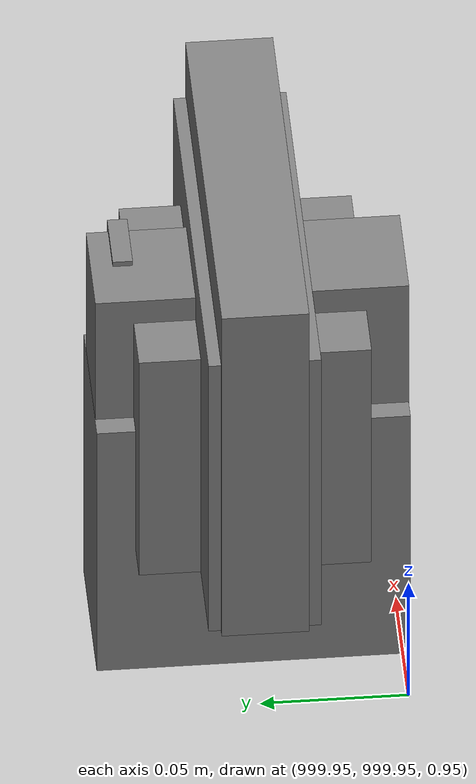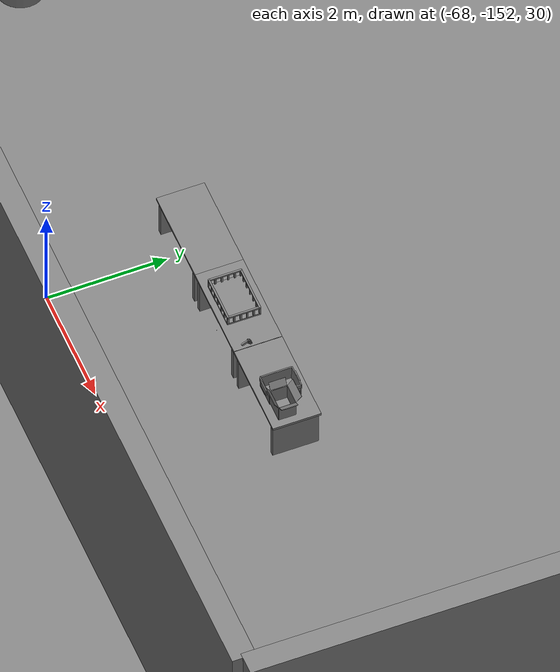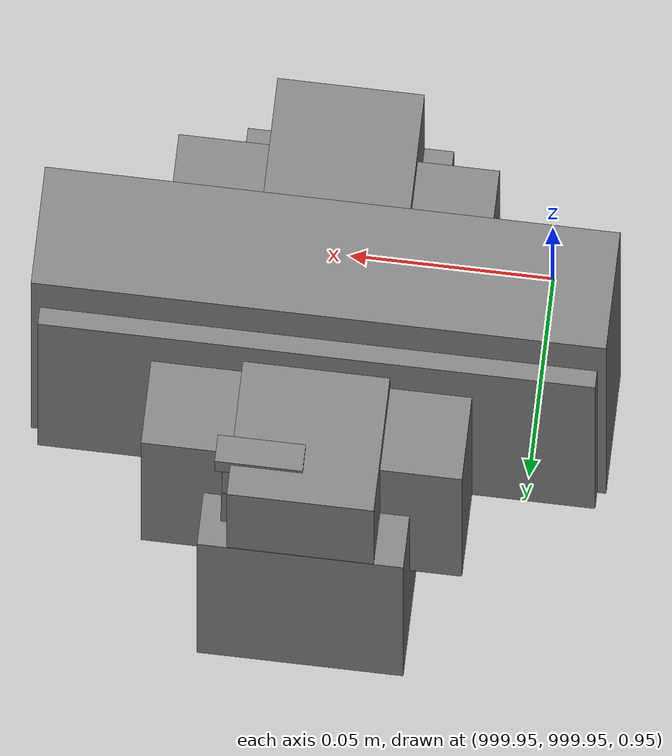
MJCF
<mujoco>
    <option gravity="0.000000000 0.000000000 -9.810000420" timestep="0.0049999999" integrator="implicitfast" density="1.225" viscosity="1.8000001e-05" noslip_iterations="10" iterations="100" sdf_iterations="50">
        <flag multiccd="disable"/>
    </option>
    <size memory="1000M"/>
    <compiler coordinate="local"/>
    <worldbody>
        <light cutoff="30" pos="0 1 1" dir="0 -1 -2"/>
        <light cutoff="30" pos="0 -1 1" dir="0 1 -2"/>
        <body pos="-64.866622925 -149.383972168 30.183746338" euler="89.999984741 89.999946594 0.000000000" name="openloong_gripper_2f85_fix_base_usda_bluebox_01">
            <geom contype="1" conaffinity="1" density="1000" type="box" material="" rgba="0.500000000 0.500000000 0.500000000 1.000000000" solimp="0.899999976 0.949999988 0.001000000" friction="1.000000000 0.005000000 0.000100000" solref="0.020000000 1.000000000" margin="0" condim="3" group="0" pos="0.276580811 0.187225342 0.000068665" quat="0.707106948 0.000077471 0.707106352 0.000077486" size="0.100000001 0.057999998 0.010000000" name="openloong_gripper_2f85_fix_base_usda_geom_3C10DB27_CD31_43E2_8C16_DB130F48200F"/>
            <geom contype="1" conaffinity="1" density="1000" type="box" material="" rgba="0.500000000 0.500000000 0.500000000 1.000000000" solimp="0.899999976 0.949999988 0.001000000" friction="1.000000000 0.005000000 0.000100000" solref="0.020000000 1.000000000" margin="0" condim="3" group="0" pos="0.000000000 0.002883911 0.000000000" quat="0.999999881 0.000000000 0.000000000 0.000000000" size="0.254000008 0.003000000 0.172000006" name="openloong_gripper_2f85_fix_base_usda_geom_ACC0ACF7_5F50_47E8_87E2_26CDD94F0727"/>
            <geom contype="1" conaffinity="1" density="1000" type="box" material="" rgba="0.500000000 0.500000000 0.500000000 1.000000000" solimp="0.899999976 0.949999988 0.001000000" friction="1.000000000 0.005000000 0.000100000" solref="0.020000000 1.000000000" margin="0" condim="3" group="0" pos="0.000000000 0.124874115 0.173484802" quat="0.999796331 0.020176515 -0.000000015 0.000000030" size="0.259999990 0.119999997 0.007000000" name="openloong_gripper_2f85_fix_base_usda_geom_8EFD8464_3F85_4257_B24C_19BB5D5A031E"/>
            <geom contype="1" conaffinity="1" density="1000" type="box" material="" rgba="0.500000000 0.500000000 0.500000000 1.000000000" solimp="0.899999976 0.949999988 0.001000000" friction="1.000000000 0.005000000 0.000100000" solref="0.020000000 1.000000000" margin="0" condim="3" group="0" pos="0.000000000 0.124874115 -0.173469543" quat="0.999796331 -0.020176545 -0.000000015 0.000000000" size="0.259999990 0.119999997 0.007000000" name="openloong_gripper_2f85_fix_base_usda_geom_71FBAC6D_3BD2_4866_BD6F_36A0783C0D0A"/>
            <geom contype="1" conaffinity="1" density="1000" type="box" material="" rgba="0.500000000 0.500000000 0.500000000 1.000000000" solimp="0.899999976 0.949999988 0.001000000" friction="1.000000000 0.005000000 0.000100000" solref="0.020000000 1.000000000" margin="0" condim="3" group="0" pos="0.000000000 0.214008331 0.188980103" quat="0.999912977 0.013176724 0.000000015 0.000000000" size="0.259999990 0.029999999 0.012500000" name="openloong_gripper_2f85_fix_base_usda_geom_CF597E04_84B9_45A7_91CA_07344E712675"/>
            <geom contype="1" conaffinity="1" density="1000" type="box" material="" rgba="0.500000000 0.500000000 0.500000000 1.000000000" solimp="0.899999976 0.949999988 0.001000000" friction="1.000000000 0.005000000 0.000100000" solref="0.020000000 1.000000000" margin="0" condim="3" group="0" pos="-0.258361816 0.125289917 0.001876831" quat="0.702796936 -0.020792112 0.710783124 0.020769298" size="0.189999998 0.119999997 0.009000000" name="openloong_gripper_2f85_fix_base_usda_geom_12114C68_F1DD_4AC3_A073_880CF5451259"/>
            <geom contype="1" conaffinity="1" density="1000" type="box" material="" rgba="0.500000000 0.500000000 0.500000000 1.000000000" solimp="0.899999976 0.949999988 0.001000000" friction="1.000000000 0.005000000 0.000100000" solref="0.020000000 1.000000000" margin="0" condim="3" group="0" pos="0.000000000 0.214008331 -0.188980103" quat="0.999912977 -0.013176769 0.000000030 0.000000015" size="0.259999990 0.029999999 0.012500000" name="openloong_gripper_2f85_fix_base_usda_geom_B7C91429_2377_44EF_B936_3C12CBFB9902"/>
            <geom contype="1" conaffinity="1" density="1000" type="box" material="" rgba="0.500000000 0.500000000 0.500000000 1.000000000" solimp="0.899999976 0.949999988 0.001000000" friction="1.000000000 0.005000000 0.000100000" solref="0.020000000 1.000000000" margin="0" condim="3" group="0" pos="-0.276611328 0.187225342 0.000068665" quat="0.707106650 0.000077441 0.707106709 0.000077456" size="0.100000001 0.057999998 0.010000000" name="openloong_gripper_2f85_fix_base_usda_geom_E310111A_A79C_4700_8CA5_A6D5B8C70393"/>
            <geom contype="1" conaffinity="1" density="1000" type="box" material="" rgba="0.500000000 0.500000000 0.500000000 1.000000000" solimp="0.899999976 0.949999988 0.001000000" friction="1.000000000 0.005000000 0.000100000" solref="0.020000000 1.000000000" margin="0" condim="3" group="0" pos="0.258331299 0.125289917 0.001876831" quat="0.702851415 0.018856421 0.710823774 -0.019329369" size="0.189999998 0.119999997 0.009000000" name="openloong_gripper_2f85_fix_base_usda_geom_2D46D3EE_468D_40B6_AF97_DB302BA719C9"/>
            <freejoint name="openloong_gripper_2f85_fix_base_usda_bluebox_01_joint"/>
            <site size="0.005000000 0.005000000 0.005000000" rgba="0.500000000 0.500000000 0.500000000 1.000000000" pos="0.000000000 0.000000000 0.000000000" quat="0.999961913 0.008726534 0.000000000 0.000000000" group="0" type="sphere" name="openloong_gripper_2f85_fix_base_usda_bluebox_01site"/>
        </body>
        <body pos="-64.496299744 -149.491867065 30.235729218" euler="0.000000000 0.000000000 89.999946594" name="openloong_gripper_2f85_fix_base_usda_cardboardbox_01">
            <geom contype="1" conaffinity="1" density="1000" type="box" material="" rgba="0.500000000 0.500000000 0.500000000 1.000000000" solimp="0.899999976 0.949999988 0.001000000" friction="1.000000000 0.005000000 0.000100000" solref="0.020000000 1.000000000" margin="0" condim="3" group="0" pos="-0.003166199 -0.004086494 0.005052090" quat="1.000000000 0.000000000 0.000000000 0.000000000" size="0.142499998 0.177500010 0.005000000" name="openloong_gripper_2f85_fix_base_usda_geom_CB89DC80_1BC4_4C67_A4F5_B98776CD00BF"/>
            <geom contype="1" conaffinity="1" density="1000" type="box" material="" rgba="0.500000000 0.500000000 0.500000000 1.000000000" solimp="0.899999976 0.949999988 0.001000000" friction="1.000000000 0.005000000 0.000100000" solref="0.020000000 1.000000000" margin="0" condim="3" group="0" pos="-0.003166199 0.170316696 0.150570869" quat="1.000000000 0.000000000 0.000000000 0.000000000" size="0.142499998 0.005000000 0.149999991" name="openloong_gripper_2f85_fix_base_usda_geom_3473FD29_9640_4542_92FB_FE5E76C5A47F"/>
            <geom contype="1" conaffinity="1" density="1000" type="box" material="" rgba="0.500000000 0.500000000 0.500000000 1.000000000" solimp="0.899999976 0.949999988 0.001000000" friction="1.000000000 0.005000000 0.000100000" solref="0.020000000 1.000000000" margin="0" condim="3" group="0" pos="-0.147399902 -0.005307198 0.150570869" quat="1.000000000 0.000000000 0.000000000 0.000000000" size="0.005000000 0.177500010 0.149999991" name="openloong_gripper_2f85_fix_base_usda_geom_2F8A752F_9FA2_4521_BA9B_81860CE9872E"/>
            <geom contype="1" conaffinity="1" density="1000" type="box" material="" rgba="0.500000000 0.500000000 0.500000000 1.000000000" solimp="0.899999976 0.949999988 0.001000000" friction="1.000000000 0.005000000 0.000100000" solref="0.020000000 1.000000000" margin="0" condim="3" group="0" pos="0.140275955 -0.005307198 0.150570869" quat="1.000000000 0.000000000 0.000000000 0.000000000" size="0.005000000 0.177500010 0.149999991" name="openloong_gripper_2f85_fix_base_usda_geom_F6ED0B35_5671_43E0_9EDB_5A0FF444D4B1"/>
            <geom contype="1" conaffinity="1" density="1000" type="box" material="" rgba="0.500000000 0.500000000 0.500000000 1.000000000" solimp="0.899999976 0.949999988 0.001000000" friction="1.000000000 0.005000000 0.000100000" solref="0.020000000 1.000000000" margin="0" condim="3" group="0" pos="-0.003166199 -0.181550980 0.150570869" quat="1.000000000 0.000000000 0.000000000 0.000000000" size="0.142499998 0.005000000 0.149999991" name="openloong_gripper_2f85_fix_base_usda_geom_7FC9890B_A248_4C7C_96B9_62B15C294BA3"/>
            <freejoint name="openloong_gripper_2f85_fix_base_usda_cardboardbox_01_joint"/>
            <site size="0.005000000 0.005000000 0.005000000" rgba="0.500000000 0.500000000 0.500000000 1.000000000" pos="0.000000000 0.000000000 0.000000000" quat="0.999961913 0.008726535 0.000000000 0.000000000" group="0" type="sphere" name="openloong_gripper_2f85_fix_base_usda_site_1B83CCB7_3C29_4E14_B08B_640A4FD72D62"/>
            <body pos="0.139160156 -0.004048347 0.301930904" euler="-179.999954224 49.383502960 179.999954224" name="openloong_gripper_2f85_fix_base_usda_A1_006">
                <geom contype="1" conaffinity="1" density="1000" type="box" material="" rgba="0.500000000 0.500000000 0.500000000 1.000000000" solimp="0.899999976 0.949999988 0.001000000" friction="1.000000000 0.005000000 0.000100000" solref="0.020000000 1.000000000" margin="0" condim="3" group="0" pos="-0.071587563 0.000009537 0.001745224" quat="0.999999881 0.000000000 0.000000000 0.000000000" size="0.071249999 0.179999992 0.002500000" name="openloong_gripper_2f85_fix_base_usda_geom_80A2D491_C3FA_40CF_AD73_6B4A464F40E0"/>
                <joint armature="0" stiffness="0.07" damping="0.0099999998" axis="0.000000 1.000000 0.000000" type="hinge" name="openloong_gripper_2f85_fix_base_usda_A1_006"/>
            </body>
            <body pos="-0.145902634 -0.004086494 0.301938057" euler="-180.000000000 -60.000011444 -180.000000000" name="openloong_gripper_2f85_fix_base_usda_A2_006">
                <geom contype="1" conaffinity="1" density="1000" type="box" material="" rgba="0.500000000 0.500000000 0.500000000 1.000000000" solimp="0.899999976 0.949999988 0.001000000" friction="1.000000000 0.005000000 0.000100000" solref="0.020000000 1.000000000" margin="0" condim="3" group="0" pos="0.071268082 0.000009537 0.002717972" quat="0.000002921 0.000000000 -0.000000030 0.999999881" size="0.071249999 0.179999992 0.002500000" name="openloong_gripper_2f85_fix_base_usda_geom_B6495048_9632_438A_8D7E_BDE4E241ECDA"/>
                <joint armature="0" stiffness="0.07" damping="0.0099999998" axis="0.000000 1.000000 0.000000" type="hinge" name="openloong_gripper_2f85_fix_base_usda_A2_006"/>
            </body>
            <body pos="-0.003385544 0.175991058 0.301930904" euler="-125.858116150 -0.000004561 0.000002331" name="openloong_gripper_2f85_fix_base_usda_B2_006">
                <geom contype="1" conaffinity="1" density="1000" type="box" material="" rgba="0.500000000 0.500000000 0.500000000 1.000000000" solimp="0.899999976 0.949999988 0.001000000" friction="1.000000000 0.005000000 0.000100000" solref="0.020000000 1.000000000" margin="0" condim="3" group="0" pos="0.000009537 -0.070939064 -0.002470016" quat="0.999614120 0.027776197 -0.000000015 0.000000030" size="0.137500003 0.064999998 0.005000000" name="openloong_gripper_2f85_fix_base_usda_geom_E9986BDB_53A2_486B_816B_A8EFD7A79E3F"/>
                <joint armature="0" stiffness="0.07" damping="0.0099999998" axis="1.000000 0.000000 0.000000" type="hinge" name="openloong_gripper_2f85_fix_base_usda_B2_006"/>
            </body>
            <body pos="-0.003385544 -0.184140205 0.301938057" euler="147.805557251 0.000000000 0.000000000" name="openloong_gripper_2f85_fix_base_usda_B1_006">
                <geom contype="1" conaffinity="1" density="1000" type="box" material="" rgba="0.500000000 0.500000000 0.500000000 1.000000000" solimp="0.899999976 0.949999988 0.001000000" friction="1.000000000 0.005000000 0.000100000" solref="0.020000000 1.000000000" margin="0" condim="3" group="0" pos="-0.000028610 0.070202351 -0.002703667" quat="0.999614179 -0.027776167 0.000000000 0.000000000" size="0.137500003 0.064999998 0.005000000" name="openloong_gripper_2f85_fix_base_usda_geom_7C273FEE_5015_4D26_AFE8_3BF7F78A79E8"/>
                <joint armature="0" stiffness="0.07" damping="0.0099999998" axis="1.000000 0.000000 0.000000" type="hinge" name="openloong_gripper_2f85_fix_base_usda_B1_006"/>
            </body>
        </body>
        <body pos="-65.882858276 -149.481979370 30.229999542" euler="-64.487716675 0.000000000 0.000000000" name="openloong_gripper_2f85_fix_base_usda_Barcode">
            <geom contype="1" conaffinity="1" density="1000" type="box" material="" rgba="0.500000000 0.500000000 0.500000000 1.000000000" solimp="0.899999976 0.949999988 0.001000000" friction="1.000000000 0.005000000 0.000100000" solref="0.020000000 1.000000000" margin="0" condim="3" group="0" pos="0.000000000 0.013038635 0.001419067" quat="0.000000000 0.000000000 0.000000000 1.000000119" size="0.034000002 0.010000000 0.017999999" name="openloong_gripper_2f85_fix_base_usda_geom_AA298D68_B4F9_49B3_BF32_4A0D0AA03BBA"/>
            <geom contype="1" conaffinity="1" density="1000" type="box" material="" rgba="0.500000000 0.500000000 0.500000000 1.000000000" solimp="0.899999976 0.949999988 0.001000000" friction="1.000000000 0.005000000 0.000100000" solref="0.020000000 1.000000000" margin="0" condim="3" group="0" pos="0.000000000 -0.035301208 -0.007095337" quat="0.000000000 0.000000000 -0.043619365 0.999048233" size="0.028999999 0.010000000 0.020000000" name="openloong_gripper_2f85_fix_base_usda_geom_726BF2F3_7C90_4659_8F82_C26978CC4D15"/>
            <geom contype="1" conaffinity="1" density="1000" type="box" material="" rgba="0.500000000 0.500000000 0.500000000 1.000000000" solimp="0.899999976 0.949999988 0.001000000" friction="1.000000000 0.005000000 0.000100000" solref="0.020000000 1.000000000" margin="0" condim="3" group="0" pos="0.000000000 -0.043411255 -0.011749268" quat="0.922262907 0.386563420 0.000000000 0.000000000" size="0.026000001 0.010000000 0.020000000" name="openloong_gripper_2f85_fix_base_usda_geom_588BBEC8_DBE0_4803_B801_1BB06968D1DD"/>
            <geom contype="1" conaffinity="1" density="1000" type="box" material="" rgba="0.500000000 0.500000000 0.500000000 1.000000000" solimp="0.899999976 0.949999988 0.001000000" friction="1.000000000 0.005000000 0.000100000" solref="0.020000000 1.000000000" margin="0" condim="3" group="0" pos="0.000000000 -0.016967773 -0.031860352" quat="0.000000000 0.000000000 0.000000000 1.000000119" size="0.008000000 0.010000000 0.013000000" name="openloong_gripper_2f85_fix_base_usda_geom_36C6A729_4000_4A14_98F5_EA65FC38AA29"/>
            <geom contype="1" conaffinity="1" density="1000" type="box" material="" rgba="0.500000000 0.500000000 0.500000000 1.000000000" solimp="0.899999976 0.949999988 0.001000000" friction="1.000000000 0.005000000 0.000100000" solref="0.020000000 1.000000000" margin="0" condim="3" group="0" pos="0.000000000 -0.001869202 0.000312805" quat="0.953716993 0.300705761 0.000000000 0.000000000" size="0.032000002 0.010000000 0.018999999" name="openloong_gripper_2f85_fix_base_usda_geom_E073FA1B_0975_430D_A639_7BC8D8719B94"/>
            <geom contype="1" conaffinity="1" density="1000" type="box" material="" rgba="0.500000000 0.500000000 0.500000000 1.000000000" solimp="0.899999976 0.949999988 0.001000000" friction="1.000000000 0.005000000 0.000100000" solref="0.020000000 1.000000000" margin="0" condim="3" group="0" pos="0.000000000 -0.019531250 -0.003173828" quat="0.953716993 0.300705761 0.000000000 0.000000000" size="0.030999999 0.010000000 0.020000000" name="openloong_gripper_2f85_fix_base_usda_geom_F4074153_5BC4_4421_87B1_F5B8E94ADFEF"/>
            <geom contype="1" conaffinity="1" density="1000" type="box" material="" rgba="0.500000000 0.500000000 0.500000000 1.000000000" solimp="0.899999976 0.949999988 0.001000000" friction="1.000000000 0.005000000 0.000100000" solref="0.020000000 1.000000000" margin="0" condim="3" group="0" pos="0.000000000 -0.035301208 -0.007095337" quat="0.953716993 0.300705761 0.000000000 0.000000000" size="0.028999999 0.010000000 0.020000000" name="openloong_gripper_2f85_fix_base_usda_geom_D4666CCB_DEEF_49AA_BAB4_3999327E86D3"/>
            <geom contype="1" conaffinity="1" density="1000" type="box" material="" rgba="0.500000000 0.500000000 0.500000000 1.000000000" solimp="0.899999976 0.949999988 0.001000000" friction="1.000000000 0.005000000 0.000100000" solref="0.020000000 1.000000000" margin="0" condim="3" group="0" pos="0.000000000 -0.042617798 -0.071121216" quat="0.000000000 0.000000000 0.000000000 1.000000119" size="0.013000000 0.021000000 0.059999999" name="openloong_gripper_2f85_fix_base_usda_geom_D356DA17_046B_483F_894B_02A40581C822"/>
            <freejoint name="openloong_gripper_2f85_fix_base_usda_Barcode_joint"/>
            <site size="0.005000000 0.005000000 0.005000000" rgba="0.500000000 0.500000000 0.500000000 1.000000000" pos="0.000000000 0.000000000 0.000000000" quat="1.000000000 0.000000000 0.000000000 0.000000000" group="0" type="sphere" name="openloong_gripper_2f85_fix_base_usda_Barcode_site"/>
        </body>
        <body pos="-66.745018005 -149.392349243 30.184000015" euler="0.000000000 0.000000000 89.999946594" name="[22330999884695]_Basket_01">
            <geom contype="1" conaffinity="1" density="1000" type="box" material="" rgba="0.500000000 0.500000000 0.500000000 1.000000000" solimp="0.899999976 0.949999988 0.001000000" friction="1.000000000 0.005000000 0.000100000" solref="0.020000000 1.000000000" margin="0" condim="3" group="0" pos="-0.052425385 0.389207840 0.089787483" quat="0.707107008 0.000000000 0.000000000 0.707106411" size="0.014249999 0.014249999 0.059999999" name="[22330999884695]_geom_EBD16DFD_F5E2_4792_887D_2254093DC1F3"/>
            <geom contype="1" conaffinity="1" density="1000" type="box" material="" rgba="0.500000000 0.500000000 0.500000000 1.000000000" solimp="0.899999976 0.949999988 0.001000000" friction="1.000000000 0.005000000 0.000100000" solref="0.020000000 1.000000000" margin="0" condim="3" group="0" pos="0.264015198 -0.133043289 0.089787483" quat="0.707107008 0.000000000 0.000000000 0.707106411" size="0.014249999 0.014249999 0.059999999" name="[22330999884695]_geom_0FFF0B5A_EDA3_452D_8B69_D3EBC5DC807F"/>
            <geom contype="1" conaffinity="1" density="1000" type="box" material="" rgba="0.500000000 0.500000000 0.500000000 1.000000000" solimp="0.899999976 0.949999988 0.001000000" friction="1.000000000 0.005000000 0.000100000" solref="0.020000000 1.000000000" margin="0" condim="3" group="0" pos="-0.264015198 -0.265548706 0.089793205" quat="0.707107008 0.000000000 0.000000000 0.707106411" size="0.014249999 0.014249999 0.059999999" name="[22330999884695]_geom_22B2BF61_47FC_492C_81A3_B99822EA548C"/>
            <geom contype="1" conaffinity="1" density="1000" type="box" material="" rgba="0.500000000 0.500000000 0.500000000 1.000000000" solimp="0.899999976 0.949999988 0.001000000" friction="1.000000000 0.005000000 0.000100000" solref="0.020000000 1.000000000" margin="0" condim="3" group="0" pos="-0.160263062 -0.389322281 0.089793205" quat="0.707107008 0.000000000 0.000000000 0.707106411" size="0.014249999 0.014249999 0.059999999" name="[22330999884695]_geom_97FA1859_3580_4F10_8AE8_B1FAB3423A73"/>
            <geom contype="1" conaffinity="1" density="1000" type="box" material="" rgba="0.500000000 0.500000000 0.500000000 1.000000000" solimp="0.899999976 0.949999988 0.001000000" friction="1.000000000 0.005000000 0.000100000" solref="0.020000000 1.000000000" margin="0" condim="3" group="0" pos="0.162265778 -0.389322281 0.089787483" quat="0.707107008 0.000000000 0.000000000 0.707106411" size="0.014249999 0.014249999 0.059999999" name="[22330999884695]_geom_C9BC8798_A49B_4B4A_AA7E_E7F1142B67EB"/>
            <geom contype="1" conaffinity="1" density="1000" type="box" material="" rgba="0.500000000 0.500000000 0.500000000 1.000000000" solimp="0.899999976 0.949999988 0.001000000" friction="1.000000000 0.005000000 0.000100000" solref="0.020000000 1.000000000" margin="0" condim="3" group="0" pos="0.264015198 0.389207840 0.089787483" quat="0.707107008 0.000000000 0.000000000 0.707106411" size="0.014249999 0.014249999 0.059999999" name="[22330999884695]_geom_96EE0E6A_F15D_480A_8EB9_ABFC4DD79265"/>
            <geom contype="1" conaffinity="1" density="1000" type="box" material="" rgba="0.500000000 0.500000000 0.500000000 1.000000000" solimp="0.899999976 0.949999988 0.001000000" friction="1.000000000 0.005000000 0.000100000" solref="0.020000000 1.000000000" margin="0" condim="3" group="0" pos="-0.264015198 -0.133043289 0.089793205" quat="0.707107008 0.000000000 0.000000000 0.707106411" size="0.014249999 0.014249999 0.059999999" name="[22330999884695]_geom_98A7D163_252E_411F_9CB1_F731CC9B8341"/>
            <geom contype="1" conaffinity="1" density="1000" type="box" material="" rgba="0.500000000 0.500000000 0.500000000 1.000000000" solimp="0.899999976 0.949999988 0.001000000" friction="1.000000000 0.005000000 0.000100000" solref="0.020000000 1.000000000" margin="0" condim="3" group="0" pos="-0.264026642 0.269256592 0.089793205" quat="0.707107008 0.000000000 0.000000000 0.707106411" size="0.014249999 0.014249999 0.059999999" name="[22330999884695]_geom_FCD472A6_9D54_4347_B179_3A153CDD2C69"/>
            <geom contype="1" conaffinity="1" density="1000" type="box" material="" rgba="0.500000000 0.500000000 0.500000000 1.000000000" solimp="0.899999976 0.949999988 0.001000000" friction="1.000000000 0.005000000 0.000100000" solref="0.020000000 1.000000000" margin="0" condim="3" group="0" pos="0.054462433 0.389207840 0.089787483" quat="0.707107008 0.000000000 0.000000000 0.707106411" size="0.014249999 0.014249999 0.059999999" name="[22330999884695]_geom_173F8699_6A1F_4B34_8C07_27B12617C601"/>
            <geom contype="1" conaffinity="1" density="1000" type="box" material="" rgba="0.500000000 0.500000000 0.500000000 1.000000000" solimp="0.899999976 0.949999988 0.001000000" friction="1.000000000 0.005000000 0.000100000" solref="0.020000000 1.000000000" margin="0" condim="3" group="0" pos="0.054462433 -0.389322281 0.089787483" quat="0.707107008 0.000000000 0.000000000 0.707106411" size="0.014249999 0.014249999 0.059999999" name="[22330999884695]_geom_B42783DE_E261_4D4C_9C2D_4BC857C12297"/>
            <geom contype="1" conaffinity="1" density="1000" type="box" material="" rgba="0.500000000 0.500000000 0.500000000 1.000000000" solimp="0.899999976 0.949999988 0.001000000" friction="1.000000000 0.005000000 0.000100000" solref="0.020000000 1.000000000" margin="0" condim="3" group="0" pos="0.264015198 0.269256592 0.089793205" quat="0.707107008 0.000000000 0.000000000 0.707106411" size="0.014249999 0.014249999 0.059999999" name="[22330999884695]_geom_19A5D968_A323_4B89_AE9C_4CD8F0D0097A"/>
            <geom contype="1" conaffinity="1" density="1000" type="box" material="" rgba="0.500000000 0.500000000 0.500000000 1.000000000" solimp="0.899999976 0.949999988 0.001000000" friction="1.000000000 0.005000000 0.000100000" solref="0.020000000 1.000000000" margin="0" condim="3" group="0" pos="0.264015198 -0.389322281 0.089787483" quat="0.707107008 0.000000000 0.000000000 0.707106411" size="0.014249999 0.014249999 0.059999999" name="[22330999884695]_geom_28CD0489_E6F6_484D_B3A7_4A9C44D53633"/>
            <geom contype="1" conaffinity="1" density="1000" type="box" material="" rgba="0.500000000 0.500000000 0.500000000 1.000000000" solimp="0.899999976 0.949999988 0.001000000" friction="1.000000000 0.005000000 0.000100000" solref="0.020000000 1.000000000" margin="0" condim="3" group="0" pos="0.000000000 0.000000000 0.015998840" quat="0.707107008 0.000000000 0.000000000 0.707106411" size="0.403499991 0.279000014 0.015750000" name="[22330999884695]_geom_06C5F19C_43C6_464A_B116_BF72F4085A1D"/>
            <geom contype="1" conaffinity="1" density="1000" type="box" material="" rgba="0.500000000 0.500000000 0.500000000 1.000000000" solimp="0.899999976 0.949999988 0.001000000" friction="1.000000000 0.005000000 0.000100000" solref="0.020000000 1.000000000" margin="0" condim="3" group="0" pos="0.000000000 -0.389476776 0.163619041" quat="0.707107008 0.000000000 0.000000000 0.707106411" size="0.015000000 0.277500004 0.015750000" name="[22330999884695]_geom_C3D1F654_D410_47CD_8DC8_28D7C3D01872"/>
            <geom contype="1" conaffinity="1" density="1000" type="box" material="" rgba="0.500000000 0.500000000 0.500000000 1.000000000" solimp="0.899999976 0.949999988 0.001000000" friction="1.000000000 0.005000000 0.000100000" solref="0.020000000 1.000000000" margin="0" condim="3" group="0" pos="0.162265778 0.389207840 0.089787483" quat="0.707107008 0.000000000 0.000000000 0.707106411" size="0.014249999 0.014249999 0.059999999" name="[22330999884695]_geom_615F2DE5_8383_4D29_80B6_33BD7A5824E0"/>
            <geom contype="1" conaffinity="1" density="1000" type="box" material="" rgba="0.500000000 0.500000000 0.500000000 1.000000000" solimp="0.899999976 0.949999988 0.001000000" friction="1.000000000 0.005000000 0.000100000" solref="0.020000000 1.000000000" margin="0" condim="3" group="0" pos="0.000000000 0.389471054 0.163619041" quat="0.707107008 0.000000000 0.000000000 0.707106411" size="0.015000000 0.277500004 0.015750000" name="[22330999884695]_geom_2E5F6C0C_D637_4547_89EE_E627484F1989"/>
            <geom contype="1" conaffinity="1" density="1000" type="box" material="" rgba="0.500000000 0.500000000 0.500000000 1.000000000" solimp="0.899999976 0.949999988 0.001000000" friction="1.000000000 0.005000000 0.000100000" solref="0.020000000 1.000000000" margin="0" condim="3" group="0" pos="-0.263511658 0.000000000 0.163619041" quat="0.707107008 0.000000000 0.000000000 0.707106411" size="0.403499991 0.015000000 0.015750000" name="[22330999884695]_geom_38341206_2A86_48D6_8F45_CF76F101052A"/>
            <geom contype="1" conaffinity="1" density="1000" type="box" material="" rgba="0.500000000 0.500000000 0.500000000 1.000000000" solimp="0.899999976 0.949999988 0.001000000" friction="1.000000000 0.005000000 0.000100000" solref="0.020000000 1.000000000" margin="0" condim="3" group="0" pos="-0.264015198 0.141334534 0.089793205" quat="0.707107008 0.000000000 0.000000000 0.707106411" size="0.014249999 0.014249999 0.059999999" name="[22330999884695]_geom_F19A5A47_19B7_48C5_B244_167C4F24620D"/>
            <geom contype="1" conaffinity="1" density="1000" type="box" material="" rgba="0.500000000 0.500000000 0.500000000 1.000000000" solimp="0.899999976 0.949999988 0.001000000" friction="1.000000000 0.005000000 0.000100000" solref="0.020000000 1.000000000" margin="0" condim="3" group="0" pos="0.264015198 -0.265548706 0.089787483" quat="0.707107008 0.000000000 0.000000000 0.707106411" size="0.014249999 0.014249999 0.059999999" name="[22330999884695]_geom_59641CA8_3610_440F_80E2_6140F4D7234B"/>
            <geom contype="1" conaffinity="1" density="1000" type="box" material="" rgba="0.500000000 0.500000000 0.500000000 1.000000000" solimp="0.899999976 0.949999988 0.001000000" friction="1.000000000 0.005000000 0.000100000" solref="0.020000000 1.000000000" margin="0" condim="3" group="0" pos="-0.160263062 0.389207840 0.089787483" quat="0.707107008 0.000000000 0.000000000 0.707106411" size="0.014249999 0.014249999 0.059999999" name="[22330999884695]_geom_8E5AA3D9_3C27_444D_A711_98267F3A7D20"/>
            <geom contype="1" conaffinity="1" density="1000" type="box" material="" rgba="0.500000000 0.500000000 0.500000000 1.000000000" solimp="0.899999976 0.949999988 0.001000000" friction="1.000000000 0.005000000 0.000100000" solref="0.020000000 1.000000000" margin="0" condim="3" group="0" pos="-0.052425385 -0.389322281 0.089787483" quat="0.707107008 0.000000000 0.000000000 0.707106411" size="0.014249999 0.014249999 0.059999999" name="[22330999884695]_geom_99C0DE11_FF6E_4D84_BD22_D42653246CA6"/>
            <geom contype="1" conaffinity="1" density="1000" type="box" material="" rgba="0.500000000 0.500000000 0.500000000 1.000000000" solimp="0.899999976 0.949999988 0.001000000" friction="1.000000000 0.005000000 0.000100000" solref="0.020000000 1.000000000" margin="0" condim="3" group="0" pos="-0.264026642 -0.389322281 0.089793205" quat="0.707107008 0.000000000 0.000000000 0.707106411" size="0.014249999 0.014249999 0.059999999" name="[22330999884695]_geom_7BC62615_D968_4E83_B3EF_379B17BB2252"/>
            <geom contype="1" conaffinity="1" density="1000" type="box" material="" rgba="0.500000000 0.500000000 0.500000000 1.000000000" solimp="0.899999976 0.949999988 0.001000000" friction="1.000000000 0.005000000 0.000100000" solref="0.020000000 1.000000000" margin="0" condim="3" group="0" pos="0.264015198 0.141334534 0.089787483" quat="0.707107008 0.000000000 0.000000000 0.707106411" size="0.014249999 0.014249999 0.059999999" name="[22330999884695]_geom_36A51B60_8557_4E0E_B7C3_F95E9FAA15E2"/>
            <geom contype="1" conaffinity="1" density="1000" type="box" material="" rgba="0.500000000 0.500000000 0.500000000 1.000000000" solimp="0.899999976 0.949999988 0.001000000" friction="1.000000000 0.005000000 0.000100000" solref="0.020000000 1.000000000" margin="0" condim="3" group="0" pos="-0.264015198 0.389207840 0.089793205" quat="0.707107008 0.000000000 0.000000000 0.707106411" size="0.014249999 0.014249999 0.059999999" name="[22330999884695]_geom_EE94BB46_BAB1_45CD_B844_776714D98EA9"/>
            <geom contype="1" conaffinity="1" density="1000" type="box" material="" rgba="0.500000000 0.500000000 0.500000000 1.000000000" solimp="0.899999976 0.949999988 0.001000000" friction="1.000000000 0.005000000 0.000100000" solref="0.020000000 1.000000000" margin="0" condim="3" group="0" pos="0.264015198 0.004480362 0.089787483" quat="0.707107008 0.000000000 0.000000000 0.707106411" size="0.014249999 0.014249999 0.059999999" name="[22330999884695]_geom_F8DCA1E8_8D86_44E7_94B2_F52507D12979"/>
            <geom contype="1" conaffinity="1" density="1000" type="box" material="" rgba="0.500000000 0.500000000 0.500000000 1.000000000" solimp="0.899999976 0.949999988 0.001000000" friction="1.000000000 0.005000000 0.000100000" solref="0.020000000 1.000000000" margin="0" condim="3" group="0" pos="0.263694763 -0.000011444 0.163619041" quat="0.707107008 0.000000000 0.000000000 0.707106411" size="0.403499991 0.015000000 0.015750000" name="[22330999884695]_geom_F0CDCB4C_87BE_45E5_ACAB_D0DB93A59F59"/>
            <geom contype="1" conaffinity="1" density="1000" type="box" material="" rgba="0.500000000 0.500000000 0.500000000 1.000000000" solimp="0.899999976 0.949999988 0.001000000" friction="1.000000000 0.005000000 0.000100000" solref="0.020000000 1.000000000" margin="0" condim="3" group="0" pos="-0.264015198 0.004480362 0.089793205" quat="0.707107008 0.000000000 0.000000000 0.707106411" size="0.014249999 0.014249999 0.059999999" name="[22330999884695]_geom_18D840F5_672B_416E_8556_39E9C2D1A314"/>
            <freejoint name="[22330999884695]_joint_ED1468E7_07C9_4D22_AB73_3E8CF0A4E8EE"/>
        </body>
        <body pos="0.000000000 0.000000000 0.000000000" euler="0.000000000 0.000000000 0.000000000" name="Static Objects_Static Objects">
            <geom contype="1" conaffinity="1" density="1000" type="box" material="" rgba="0.500000000 0.500000000 0.500000000 1.000000000" solimp="0.899999976 0.949999988 0.001000000" friction="1.000000000 0.005000000 0.000100000" solref="0.020000000 1.000000000" margin="0" condim="3" group="0" pos="-67.544113159 -149.365814209 29.727830887" quat="0.500000417 0.499999970 0.499999553 0.499999970" size="0.381000012 0.319999993 0.041000001" name="Static Objects_geom_D2092176_F2DE_40B7_A548_F1C8F60FE7CA"/>
            <geom contype="1" conaffinity="1" density="1000" type="box" material="" rgba="0.500000000 0.500000000 0.500000000 1.000000000" solimp="0.899999976 0.949999988 0.001000000" friction="1.000000000 0.005000000 0.000100000" solref="0.020000000 1.000000000" margin="0" condim="3" group="0" pos="-68.239501953 -149.365814209 30.086868286" quat="0.500000417 0.499999970 0.499999553 0.499999970" size="0.370999992 0.039500002 0.745000005" name="Static Objects_geom_C7A817A6_024E_4FB8_89F6_85AEBF452D1E"/>
            <geom contype="1" conaffinity="1" density="1000" type="box" material="" rgba="0.500000000 0.500000000 0.500000000 1.000000000" solimp="0.899999976 0.949999988 0.001000000" friction="1.000000000 0.005000000 0.000100000" solref="0.020000000 1.000000000" margin="0" condim="3" group="0" pos="-68.239501953 -149.365814209 30.147235870" quat="0.500000417 0.499999970 0.499999553 0.499999970" size="0.400000006 0.022000000 0.800000012" name="Static Objects_geom_178BBBC9_5A3F_4D4B_AA11_DEE9CCAC4BF2"/>
            <geom contype="1" conaffinity="1" density="1000" type="box" material="" rgba="0.500000000 0.500000000 0.500000000 1.000000000" solimp="0.899999976 0.949999988 0.001000000" friction="1.000000000 0.005000000 0.000100000" solref="0.020000000 1.000000000" margin="0" condim="3" group="0" pos="-68.934890747 -149.365814209 29.727830887" quat="0.500000417 0.499999970 0.499999553 0.499999970" size="0.381000012 0.319999993 0.041000001" name="Static Objects_geom_C9CC74AC_C4F2_4A93_B451_7106E10E8757"/>
            <geom contype="1" conaffinity="1" density="1000" type="box" material="" rgba="0.500000000 0.500000000 0.500000000 1.000000000" solimp="0.899999976 0.949999988 0.001000000" friction="1.000000000 0.005000000 0.000100000" solref="0.020000000 1.000000000" margin="0" condim="3" group="0" pos="-68.239501953 -149.365814209 29.561563492" quat="0.500000417 0.499999970 0.499999553 0.499999970" size="0.020000000 0.022000000 0.660000026" name="Static Objects_geom_D3ADF872_8FAF_4BBA_8389_2A00DCA91BDC"/>
            <geom contype="1" conaffinity="1" density="1000" type="box" material="" rgba="0.500000000 0.500000000 0.500000000 1.000000000" solimp="0.899999976 0.949999988 0.001000000" friction="1.000000000 0.005000000 0.000100000" solref="0.020000000 1.000000000" margin="0" condim="3" group="0" pos="-65.945671082 -149.365814209 29.727830887" quat="0.500000417 0.499999970 0.499999553 0.499999970" size="0.381000012 0.319999993 0.041000001" name="Static Objects_geom_4A92F847_612A_472B_AA3F_F199E4EDEF62"/>
            <geom contype="1" conaffinity="1" density="1000" type="box" material="" rgba="0.500000000 0.500000000 0.500000000 1.000000000" solimp="0.899999976 0.949999988 0.001000000" friction="1.000000000 0.005000000 0.000100000" solref="0.020000000 1.000000000" margin="0" condim="3" group="0" pos="-66.641059875 -149.365814209 30.086868286" quat="0.500000417 0.499999970 0.499999553 0.499999970" size="0.370999992 0.039500002 0.745000005" name="Static Objects_geom_38D75B72_393E_4833_9F20_ED6F7BD1FB9A"/>
            <geom contype="1" conaffinity="1" density="1000" type="box" material="" rgba="0.500000000 0.500000000 0.500000000 1.000000000" solimp="0.899999976 0.949999988 0.001000000" friction="1.000000000 0.005000000 0.000100000" solref="0.020000000 1.000000000" margin="0" condim="3" group="0" pos="-66.641059875 -149.365814209 30.147235870" quat="0.500000417 0.499999970 0.499999553 0.499999970" size="0.400000006 0.022000000 0.800000012" name="Static Objects_geom_76D91CB2_1C8E_4E0E_B75B_7483F86CA582"/>
            <geom contype="1" conaffinity="1" density="1000" type="box" material="" rgba="0.500000000 0.500000000 0.500000000 1.000000000" solimp="0.899999976 0.949999988 0.001000000" friction="1.000000000 0.005000000 0.000100000" solref="0.020000000 1.000000000" margin="0" condim="3" group="0" pos="-67.336448669 -149.365814209 29.727830887" quat="0.500000417 0.499999970 0.499999553 0.499999970" size="0.381000012 0.319999993 0.041000001" name="Static Objects_geom_318061F1_425B_4154_9DA4_16DA8EBEA27D"/>
            <geom contype="1" conaffinity="1" density="1000" type="box" material="" rgba="0.500000000 0.500000000 0.500000000 1.000000000" solimp="0.899999976 0.949999988 0.001000000" friction="1.000000000 0.005000000 0.000100000" solref="0.020000000 1.000000000" margin="0" condim="3" group="0" pos="-66.641059875 -149.365814209 29.561563492" quat="0.500000417 0.499999970 0.499999553 0.499999970" size="0.020000000 0.022000000 0.660000026" name="Static Objects_geom_480BC4D1_610B_49D7_AB14_4B48C2D19A1A"/>
            <geom contype="1" conaffinity="1" density="1000" type="box" material="" rgba="0.500000000 0.500000000 0.500000000 1.000000000" solimp="0.899999976 0.949999988 0.001000000" friction="1.000000000 0.005000000 0.000100000" solref="0.020000000 1.000000000" margin="0" condim="3" group="0" pos="-64.338577271 -149.365814209 29.727830887" quat="0.500000417 0.499999970 0.499999553 0.499999970" size="0.381000012 0.319999993 0.041000001" name="Static Objects_geom_B455CCB8_FBE7_48F5_B986_423D58489B1D"/>
            <geom contype="1" conaffinity="1" density="1000" type="box" material="" rgba="0.500000000 0.500000000 0.500000000 1.000000000" solimp="0.899999976 0.949999988 0.001000000" friction="1.000000000 0.005000000 0.000100000" solref="0.020000000 1.000000000" margin="0" condim="3" group="0" pos="-65.033966064 -149.365814209 30.086868286" quat="0.500000417 0.499999970 0.499999553 0.499999970" size="0.370999992 0.039500002 0.745000005" name="Static Objects_geom_A6B0128D_E51C_453F_B782_B4C1DA28B818"/>
            <geom contype="1" conaffinity="1" density="1000" type="box" material="" rgba="0.500000000 0.500000000 0.500000000 1.000000000" solimp="0.899999976 0.949999988 0.001000000" friction="1.000000000 0.005000000 0.000100000" solref="0.020000000 1.000000000" margin="0" condim="3" group="0" pos="-65.033966064 -149.365814209 30.147235870" quat="0.500000417 0.499999970 0.499999553 0.499999970" size="0.400000006 0.022000000 0.800000012" name="Static Objects_geom_935DF65D_B1E8_4007_ABB8_CA02D78B4C6C"/>
            <geom contype="1" conaffinity="1" density="1000" type="box" material="" rgba="0.500000000 0.500000000 0.500000000 1.000000000" solimp="0.899999976 0.949999988 0.001000000" friction="1.000000000 0.005000000 0.000100000" solref="0.020000000 1.000000000" margin="0" condim="3" group="0" pos="-65.729354858 -149.365814209 29.727830887" quat="0.500000417 0.499999970 0.499999553 0.499999970" size="0.381000012 0.319999993 0.041000001" name="Static Objects_geom_5496D81C_286A_4336_A66D_2190146F901B"/>
            <geom contype="1" conaffinity="1" density="1000" type="box" material="" rgba="0.500000000 0.500000000 0.500000000 1.000000000" solimp="0.899999976 0.949999988 0.001000000" friction="1.000000000 0.005000000 0.000100000" solref="0.020000000 1.000000000" margin="0" condim="3" group="0" pos="-65.033966064 -149.365814209 29.561563492" quat="0.500000417 0.499999970 0.499999553 0.499999970" size="0.020000000 0.022000000 0.660000026" name="Static Objects_geom_E3C0C1FF_9F57_4B2D_820D_FDE8B489FF30"/>
            <geom contype="1" conaffinity="1" density="1000" type="box" material="" rgba="0.500000000 0.500000000 0.500000000 1.000000000" solimp="0.899999976 0.949999988 0.001000000" friction="1.000000000 0.005000000 0.000100000" solref="0.020000000 1.000000000" margin="0" condim="3" group="0" pos="-61.754566193 -137.853729248 33.906845093" quat="0.707107067 0.000000000 0.000000000 0.707106471" size="0.759999990 0.759999990 4.500000000" name="Static Objects_geom_81A9DC28_47E5_4453_8DB0_E417611A0269"/>
            <geom contype="1" conaffinity="1" density="1000" type="box" material="" rgba="0.500000000 0.500000000 0.500000000 1.000000000" solimp="0.899999976 0.949999988 0.001000000" friction="1.000000000 0.005000000 0.000100000" solref="0.020000000 1.000000000" margin="0" condim="3" group="0" pos="-57.511135101 -144.927108765 31.707921982" quat="1.000000000 0.000000000 0.000000000 0.000000000" size="0.200000003 8.000000000 2.299999952" name="Static Objects_geom_9D8AF445_6C1C_44FE_91F2_FC06FBFA90E1"/>
            <geom contype="1" conaffinity="1" density="1000" type="box" material="" rgba="0.500000000 0.500000000 0.500000000 1.000000000" solimp="0.899999976 0.949999988 0.001000000" friction="1.000000000 0.005000000 0.000100000" solref="0.020000000 1.000000000" margin="0" condim="3" group="0" pos="-80.517646790 -157.574050903 31.688196182" quat="0.707107067 0.000000000 0.000000000 0.707106471" size="0.600000024 0.600000024 2.299999952" name="Static Objects_geom_EB5D2277_EF0D_4AFE_9C20_D4BA789FE157"/>
            <geom contype="1" conaffinity="1" density="1000" type="box" material="" rgba="0.500000000 0.500000000 0.500000000 1.000000000" solimp="0.899999976 0.949999988 0.001000000" friction="1.000000000 0.005000000 0.000100000" solref="0.020000000 1.000000000" margin="0" condim="3" group="0" pos="-80.711044312 -147.414932251 31.666158676" quat="1.000000000 0.000000000 0.000000000 0.000000000" size="0.200000003 10.000000000 2.299999952" name="Static Objects_geom_6FEF85BD_6DB7_4670_8266_141767FECF29"/>
            <geom contype="1" conaffinity="1" density="1000" type="box" material="" rgba="0.500000000 0.500000000 0.500000000 1.000000000" solimp="0.899999976 0.949999988 0.001000000" friction="1.000000000 0.005000000 0.000100000" solref="0.020000000 1.000000000" margin="0" condim="3" group="0" pos="-57.687217712 -137.434692383 31.688196182" quat="0.707107067 0.000000000 0.000000000 0.707106471" size="0.600000024 0.600000024 2.299999952" name="Static Objects_geom_05FE74CA_CA48_473D_A40A_F581B36073B1"/>
            <geom contype="1" conaffinity="1" density="1000" type="box" material="" rgba="0.500000000 0.500000000 0.500000000 1.000000000" solimp="0.899999976 0.949999988 0.001000000" friction="1.000000000 0.005000000 0.000100000" solref="0.020000000 1.000000000" margin="0" condim="3" group="0" pos="-69.537033081 -140.263229370 31.714921951" quat="0.707107067 0.000000000 0.000000000 0.707106471" size="0.759999990 4.500000000 2.299999952" name="Static Objects_geom_5A2EFE01_3D56_497A_9A08_9035760FC879"/>
            <geom contype="1" conaffinity="1" density="1000" type="box" material="" rgba="0.500000000 0.500000000 0.500000000 1.000000000" solimp="0.899999976 0.949999988 0.001000000" friction="1.000000000 0.005000000 0.000100000" solref="0.020000000 1.000000000" margin="0" condim="3" group="0" pos="-80.073638916 -137.853713989 33.906845093" quat="0.707107067 0.000000000 0.000000000 0.707106471" size="0.759999990 0.759999990 4.500000000" name="Static Objects_geom_B2A8852B_9CB8_45D9_AD1E_B494DB4D541A"/>
            <geom contype="1" conaffinity="1" density="1000" type="box" material="" rgba="0.500000000 0.500000000 0.500000000 1.000000000" solimp="0.899999976 0.949999988 0.001000000" friction="1.000000000 0.005000000 0.000100000" solref="0.020000000 1.000000000" margin="0" condim="3" group="0" pos="-73.406707764 -155.734664917 31.707921982" quat="1.000000000 0.000000000 0.000000000 0.000000000" size="0.200000003 3.000000000 2.299999952" name="Static Objects_geom_9D276A21_E48B_4B23_87B8_46BB20778E6A"/>
            <geom contype="1" conaffinity="1" density="1000" type="box" material="" rgba="0.500000000 0.500000000 0.500000000 1.000000000" solimp="0.899999976 0.949999988 0.001000000" friction="1.000000000 0.005000000 0.000100000" solref="0.020000000 1.000000000" margin="0" condim="3" group="0" pos="-68.497543335 -137.448257446 31.707921982" quat="0.707107067 0.000000000 0.000000000 0.707106471" size="0.200000003 14.000000000 2.299999952" name="Static Objects_geom_D61046DB_895A_4F39_9C00_4BF5AE672F9C"/>
            <geom contype="1" conaffinity="1" density="1000" type="cylinder" material="" rgba="0.500000000 0.500000000 0.500000000 1.000000000" solimp="0.899999976 0.949999988 0.001000000" friction="1.000000000 0.005000000 0.000100000" solref="0.020000000 1.000000000" margin="0" condim="3" group="0" pos="-68.868522644 -142.134506226 31.711090088" quat="0.707107067 0.000000000 0.000000000 0.707106471" size="0.509999990 2.299999952 1.000000000" name="Static Objects_geom_0BCD3AC3_6877_496A_B3B7_5FEC68D0A9BD"/>
            <geom contype="1" conaffinity="1" density="1000" type="plane" material="" rgba="0.500000000 0.500000000 0.500000000 1.000000000" solimp="0.899999976 0.949999988 0.001000000" friction="1.000000000 0.005000000 0.000100000" solref="0.020000000 1.000000000" margin="0" condim="3" group="0" pos="-72.873703003 -147.131927490 29.409669876" quat="1.000000000 0.000000000 0.000000000 0.000000000" size="18.000000000 14.000000000 1.000000000" name="Static Objects_geom_233C03FC_B45F_4C70_A7A3_9AA3C5D96E59"/>
            <geom contype="1" conaffinity="1" density="1000" type="box" material="" rgba="0.500000000 0.500000000 0.500000000 1.000000000" solimp="0.899999976 0.949999988 0.001000000" friction="1.000000000 0.005000000 0.000100000" solref="0.020000000 1.000000000" margin="0" condim="3" group="0" pos="-79.943580627 -157.782272339 31.707921982" quat="0.707107067 0.000000000 0.000000000 0.707106471" size="0.200000003 7.000000000 2.299999952" name="Static Objects_geom_203BFB01_137D_41A8_9666_BCE552B16DE1"/>
            <geom contype="1" conaffinity="1" density="1000" type="box" material="" rgba="0.500000000 0.500000000 0.500000000 1.000000000" solimp="0.899999976 0.949999988 0.001000000" friction="1.000000000 0.005000000 0.000100000" solref="0.020000000 1.000000000" margin="0" condim="3" group="0" pos="-65.421028137 -152.903442383 31.707921982" quat="0.707107067 0.000000000 0.000000000 0.707106471" size="0.200000003 7.800000191 2.299999952" name="Static Objects_geom_5B3DF97E_AE04_4BA7_8366_B300F1B82E0C"/>
            <geom contype="1" conaffinity="1" density="1000" type="box" material="" rgba="0.500000000 0.500000000 0.500000000 1.000000000" solimp="0.899999976 0.949999988 0.001000000" friction="1.000000000 0.005000000 0.000100000" solref="0.020000000 1.000000000" margin="0" condim="3" group="0" pos="-74.776908875 -149.964416504 31.688196182" quat="1.000000000 0.000000000 0.000000000 0.000000000" size="0.600000024 0.409999996 2.299999952" name="Static Objects_geom_4A808E4D_713F_4C2B_BA07_76366A3E6C55"/>
            <geom contype="1" conaffinity="1" density="1000" type="cylinder" material="" rgba="0.500000000 0.500000000 0.500000000 1.000000000" solimp="0.899999976 0.949999988 0.001000000" friction="1.000000000 0.005000000 0.000100000" solref="0.020000000 1.000000000" margin="0" condim="3" group="0" pos="-60.161884308 -142.134506226 31.711090088" quat="0.707107067 0.000000000 0.000000000 0.707106471" size="0.509999990 2.299999952 1.000000000" name="Static Objects_geom_7D1A6BD0_87AF_4302_844F_1524C3342A29"/>
            <geom contype="1" conaffinity="1" density="1000" type="cylinder" material="" rgba="0.500000000 0.500000000 0.500000000 1.000000000" solimp="0.899999976 0.949999988 0.001000000" friction="1.000000000 0.005000000 0.000100000" solref="0.020000000 1.000000000" margin="0" condim="3" group="0" pos="-75.382453918 -149.963455200 31.711090088" quat="0.707107067 0.000000000 0.000000000 0.707106471" size="0.409999996 2.299999952 1.000000000" name="Static Objects_geom_BD9FD5B5_921E_493F_970C_BA9C816DC898"/>
            <geom contype="1" conaffinity="1" density="1000" type="cylinder" material="" rgba="0.500000000 0.500000000 0.500000000 1.000000000" solimp="0.899999976 0.949999988 0.001000000" friction="1.000000000 0.005000000 0.000100000" solref="0.020000000 1.000000000" margin="0" condim="3" group="0" pos="-74.154960632 -149.963455200 31.711090088" quat="0.707107067 0.000000000 0.000000000 0.707106471" size="0.409999996 2.299999952 1.000000000" name="Static Objects_geom_134B6F8E_E852_4F00_9B89_232CC8F792AE"/>
            <geom contype="1" conaffinity="1" density="1000" type="cylinder" material="" rgba="0.500000000 0.500000000 0.500000000 1.000000000" solimp="0.899999976 0.949999988 0.001000000" friction="1.000000000 0.005000000 0.000100000" solref="0.020000000 1.000000000" margin="0" condim="3" group="0" pos="-77.566612244 -142.134506226 31.711090088" quat="0.707107067 0.000000000 0.000000000 0.707106471" size="0.509999990 2.299999952 1.000000000" name="Static Objects_geom_ADBC5B76_AF13_4A2E_8D95_AC49835A7A87"/>
        </body>
        <body pos="1000.000000000 1000.000000000 1.000000000" euler="0.000000000 0.000000000 180.000000000" name="openloong_gripper_2f85_fix_base_usda_cpu_fan">
            <geom contype="1" conaffinity="1" density="1000" type="box" material="" rgba="0.500000000 0.500000000 0.500000000 1.000000000" solimp="0.899999976 0.949999988 0.001000000" friction="1.000000000 0.005000000 0.000100000" solref="0.020000000 1.000000000" margin="0" condim="3" group="0" pos="0.000000000 0.000000000 0.070034981" quat="0.000000000 0.000000000 0.000000000 1.000000000" size="0.070700005 0.014699999 0.070700005" name="openloong_gripper_2f85_fix_base_usda_geom_5D9B833B_8016_4C42_8049_11F975B1019E"/>
            <freejoint name="openloong_gripper_2f85_fix_base_usda_cpu_fan_joint"/>
            <site size="0.005000000 0.005000000 0.005000000" rgba="0.500000000 0.500000000 0.500000000 1.000000000" pos="0.000000000 0.000000000 0.000000000" quat="0.999961913 0.008726535 0.000000000 0.000000000" group="0" type="sphere" name="openloong_gripper_2f85_fix_base_usda_cpu_fancsite"/>
        </body>
        <body pos="-66.156906128 -148.886154175 31.163103104" euler="-110.365341187 -76.152610779 -70.066986084" mocap="true" name="spotlight3_SpotLight"/>
        <body pos="1000.000000000 1000.000000000 1.000000000" euler="0.000000000 0.000000000 180.000000000" name="openloong_gripper_2f85_fix_base_usda_battery_01">
            <geom contype="1" conaffinity="1" density="1000" type="box" material="" rgba="0.500000000 0.500000000 0.500000000 1.000000000" solimp="0.899999976 0.949999988 0.001000000" friction="1.000000000 0.005000000 0.000100000" solref="0.020000000 1.000000000" margin="0" condim="3" group="0" pos="-0.011123657 -0.041940309 0.101691343" quat="1.000000000 0.000000000 0.000000000 0.000000000" size="0.010800000 0.003375000 0.004725000" name="openloong_gripper_2f85_fix_base_usda_geom_27A61A53_6A13_4DCC_B97B_A0EB1A214C60"/>
            <geom contype="1" conaffinity="1" density="1000" type="box" material="" rgba="0.500000000 0.500000000 0.500000000 1.000000000" solimp="0.899999976 0.949999988 0.001000000" friction="1.000000000 0.005000000 0.000100000" solref="0.020000000 1.000000000" margin="0" condim="3" group="0" pos="-0.010876465 -0.044247437 0.047066893" quat="0.998702705 -0.050920475 0.000000000 0.000000000" size="0.009450001 0.002700000 0.024975000" name="openloong_gripper_2f85_fix_base_usda_geom_4282C4C1_05F1_415D_819A_AA1A32ECEAB2"/>
            <geom contype="1" conaffinity="1" density="1000" type="box" material="" rgba="0.500000000 0.500000000 0.500000000 1.000000000" solimp="0.899999976 0.949999988 0.001000000" friction="1.000000000 0.005000000 0.000100000" solref="0.020000000 1.000000000" margin="0" condim="3" group="0" pos="-0.001235962 -0.000659180 0.047381196" quat="1.000000000 0.000000000 0.000000000 0.000000000" size="0.039420001 0.039150000 0.047250003" name="openloong_gripper_2f85_fix_base_usda_geom_83864CF8_49CE_44F8_83F8_1D37BAD6D882"/>
            <geom contype="1" conaffinity="1" density="1000" type="box" material="" rgba="0.500000000 0.500000000 0.500000000 1.000000000" solimp="0.899999976 0.949999988 0.001000000" friction="1.000000000 0.005000000 0.000100000" solref="0.020000000 1.000000000" margin="0" condim="3" group="0" pos="-0.010876465 -0.039138794 0.009851727" quat="1.000000000 0.000000000 0.000000000 0.000000000" size="0.009450001 0.010800000 0.013500000" name="openloong_gripper_2f85_fix_base_usda_geom_BB6186DE_D638_4952_A365_8231BC45CFA0"/>
            <geom contype="1" conaffinity="1" density="1000" type="box" material="" rgba="0.500000000 0.500000000 0.500000000 1.000000000" solimp="0.899999976 0.949999988 0.001000000" friction="1.000000000 0.005000000 0.000100000" solref="0.020000000 1.000000000" margin="0" condim="3" group="0" pos="-0.010876465 -0.041528322 0.071508206" quat="1.000000000 0.000000000 0.000000000 0.000000000" size="0.009450001 0.002700000 0.027000001" name="openloong_gripper_2f85_fix_base_usda_geom_FA57F029_57B2_42F3_86C7_2CA1FE7841E1"/>
            <freejoint name="openloong_gripper_2f85_fix_base_usda_battery_01_joint"/>
            <site size="0.005000000 0.005000000 0.005000000" rgba="0.500000000 0.500000000 0.500000000 1.000000000" pos="0.000000000 0.000000000 0.000000000" quat="0.999961913 0.008726500 0.000000000 0.000000000" group="0" type="sphere" name="openloong_gripper_2f85_fix_base_usda_battery_01site"/>
        </body>
        <body pos="-66.069694519 -149.593460083 31.162899017" euler="157.690277100 46.617172241 160.531967163" mocap="true" name="spotlight2_SpotLight"/>
        <body pos="-66.076087952 -149.410385132 31.163465500" euler="97.202583313 76.217491150 34.272331238" mocap="true" name="spotlight1_SpotLight"/>
        <body pos="1000.000000000 1000.000000000 1.000000000" euler="0.000000000 0.000000000 180.000000000" name="openloong_gripper_2f85_fix_base_usda_wifi_box">
            <geom contype="1" conaffinity="1" density="1000" type="box" material="" rgba="0.500000000 0.500000000 0.500000000 1.000000000" solimp="0.899999976 0.949999988 0.001000000" friction="1.000000000 0.005000000 0.000100000" solref="0.020000000 1.000000000" margin="0" condim="3" group="0" pos="0.000000000 0.000000000 0.058978677" quat="0.000000000 0.000000047 0.000000000 1.000000000" size="0.068499997 0.018999999 0.059000000" name="openloong_gripper_2f85_fix_base_usda_geom_4A5FE7DF_FE9C_4673_94D8_2167B9B8545D"/>
            <freejoint name="openloong_gripper_2f85_fix_base_usda_wifi_box_joint"/>
            <site size="0.005000000 0.005000000 0.005000000" rgba="0.500000000 0.500000000 0.500000000 1.000000000" pos="0.000000000 0.000000000 0.000000000" quat="0.999961913 0.008726500 0.000000000 0.000000000" group="0" type="sphere" name="openloong_gripper_2f85_fix_base_usda_wifi_boxsite"/>
        </body>
        <body pos="1000.000000000 1000.000000000 1.000000000" euler="0.000011953 0.000005123 -179.999984741" name="openloong_gripper_2f85_fix_base_usda_intel_box">
            <geom contype="1" conaffinity="1" density="1000" type="box" material="" rgba="0.500000000 0.500000000 0.500000000 1.000000000" solimp="0.899999976 0.949999988 0.001000000" friction="1.000000000 0.005000000 0.000100000" solref="0.020000000 1.000000000" margin="0" condim="3" group="0" pos="0.000000000 -0.000067139 0.000082284" quat="0.707106709 0.000000225 0.000000253 0.707106650" size="0.052800003 0.025300000 0.052800003" name="openloong_gripper_2f85_fix_base_usda_geom_0932958C_7E81_4AFA_9390_FA592BBE7319"/>
            <freejoint name="openloong_gripper_2f85_fix_base_usda_intel_box_joint"/>
            <site size="0.005000000 0.005000000 0.005000000" rgba="0.500000000 0.500000000 0.500000000 1.000000000" pos="0.000000000 0.000000000 0.000000000" quat="0.999961913 0.008726500 0.000000000 0.000000000" group="0" type="sphere" name="openloong_gripper_2f85_fix_base_usda_intel_boxsite"/>
        </body>
        <body pos="1000.000000000 999.999938965 1.000000000" euler="0.000000000 0.000000000 180.000000000" name="openloong_gripper_2f85_fix_base_usda_intelcore_i5">
            <geom contype="1" conaffinity="1" density="1000" type="box" material="" rgba="0.500000000 0.500000000 0.500000000 1.000000000" solimp="0.899999976 0.949999988 0.001000000" friction="1.000000000 0.005000000 0.000100000" solref="0.020000000 1.000000000" margin="0" condim="3" group="0" pos="0.000000000 0.000000000 0.051722717" quat="0.707106709 0.000000000 0.000000000 -0.707106769" size="0.052800000 0.018080002 0.052800000" name="openloong_gripper_2f85_fix_base_usda_geom_1F42EE3D_325C_43AB_9147_7D74F0F97C6E"/>
            <freejoint name="openloong_gripper_2f85_fix_base_usda_intelcore_i5_joint"/>
            <site size="0.005000000 0.005000000 0.005000000" rgba="0.500000000 0.500000000 0.500000000 1.000000000" pos="0.000000000 0.000000000 0.000000000" quat="0.999961913 0.008726534 0.000000000 0.000000000" group="0" type="sphere" name="openloong_gripper_2f85_fix_base_usda_intelcore_i5site"/>
        </body>
        <body pos="-66.291030884 -149.869689941 29.018842697" euler="0.000000000 0.000000000 89.999946594" mocap="true" name="openloong_gripper_2f85_fix_base_usda_leftHandMocap"/>
        <body pos="-66.291030884 -149.869689941 29.018842697" euler="0.000000000 0.000000000 89.999946594" mocap="true" name="openloong_gripper_2f85_fix_base_usda_rightHandMocap"/>
        <body pos="-66.291030884 -149.869689941 30.218843460" euler="0.000000000 0.000000000 89.999946594" name="openloong_gripper_2f85_fix_base_usda_base_link">
            <geom contype="1" conaffinity="1" density="1000" type="mesh" material="" rgba="0.783999979 0.783999979 0.783999979 1.000000000" solimp="0.899999976 0.949999988 0.001000000" friction="1.000000000 0.005000000 0.000100000" solref="0.020000000 1.000000000" margin="0" condim="3" group="3" mesh="base_link" pos="0.000000000 0.000000000 0.000000000" quat="1.000000000 0.000000000 0.000000000 0.000000000" size="1.000000000 1.000000000 1.000000000" name="openloong_gripper_2f85_fix_base_usda__geom_7_23EB98E1_B202_427C_AB9F_C6B6B248944E"/>
            <site size="0.005000000 0.005000000 0.005000000" rgba="0.500000000 0.500000000 0.500000000 1.000000000" pos="0.000000000 0.000000000 0.000000000" quat="1.000000000 0.000000000 0.000000000 0.000000000" group="0" type="sphere" name="openloong_gripper_2f85_fix_base_usda_imu"/>
            <inertial mass="22.447001" pos="-0.005664100 -0.001336700 0.238289997" diaginertia="0.374352545 0.277180195 0.220617250" quat="0.999247074 0.035235517 -0.015086859 0.006023135"/>
            <body pos="0.000000000 0.000000000 0.299997330" euler="0.000000000 0.000000000 0.000000000" name="openloong_gripper_2f85_fix_base_usda_dummy_body">
                <geom contype="1" conaffinity="1" density="1000" type="sphere" material="" rgba="0.783999979 0.783999979 0.783999979 1.000000000" solimp="0.899999976 0.949999988 0.001000000" friction="1.000000000 0.005000000 0.000100000" solref="0.020000000 1.000000000" margin="0" condim="3" group="3" pos="0.000000000 0.000000000 0.000000000" quat="1.000000000 0.000000000 0.000000000 0.000000000" size="0.010000000 0.000000000 0.000000000" name="openloong_gripper_2f85_fix_base_usda__geom_8_39AB1C59_15A4_4077_901E_CD4DBDB3210A"/>
                <joint armature="0.0099999998" stiffness="0" damping="0.1" axis="0.000000 0.000000 1.000000" type="hinge" name="openloong_gripper_2f85_fix_base_usda_dummy_joint"/>
                <site size="0.010000000 0.005000000 0.005000000" rgba="0.500000000 0.500000000 0.500000000 1.000000000" pos="0.000000000 0.000000000 0.000000000" quat="1.000000000 0.000000000 0.000000000 0.000000000" group="3" type="sphere" name="openloong_gripper_2f85_fix_base_usda_dummy_site"/>
            </body>
            <body pos="0.009002686 0.000000000 0.406400681" euler="0.000000000 0.000000000 0.000000000" name="openloong_gripper_2f85_fix_base_usda_Link_head_yaw">
                <geom contype="1" conaffinity="1" density="1000" type="mesh" material="" rgba="0.783999979 0.783999979 0.783999979 1.000000000" solimp="0.899999976 0.949999988 0.001000000" friction="1.000000000 0.005000000 0.000100000" solref="0.020000000 1.000000000" margin="0" condim="3" group="3" mesh="Link_head_yaw" pos="0.000000000 0.000000000 0.000000000" quat="1.000000000 0.000000000 0.000000000 0.000000000" size="1.000000000 1.000000000 1.000000000" name="openloong_gripper_2f85_fix_base_usda__geom_10_160C6A34_2B1D_4965_ADAE_A205DDEFCB94"/>
                <inertial mass="0.84249002" pos="0.000000000 -0.002081400 0.044801001" diaginertia="0.000700588 0.000629000 0.000553812" quat="0.706933022 -0.015675601 0.015677100 0.706933022"/>
                <body pos="0.000000000 -0.034599304 0.048500061" euler="0.000000000 0.000000000 0.000000000" name="openloong_gripper_2f85_fix_base_usda_Link_head_pitch">
                    <geom contype="1" conaffinity="1" density="1000" type="mesh" material="" rgba="0.783999979 0.783999979 0.783999979 1.000000000" solimp="0.899999976 0.949999988 0.001000000" friction="1.000000000 0.005000000 0.000100000" solref="0.020000000 1.000000000" margin="0" condim="3" group="3" mesh="Link_head_pitch" pos="0.000000000 0.000000000 0.000000000" quat="1.000000000 0.000000000 0.000000000 0.000000000" size="1.000000000 1.000000000 1.000000000" name="openloong_gripper_2f85_fix_base_usda__geom_12_35A7134C_37C8_4817_A7C3_0AC37D859605"/>
                    <inertial mass="1.3943" pos="0.020569000 0.033004001 0.125000000" diaginertia="0.006381400 0.006289940 0.004481460" quat="0.973390222 0.008406822 0.228157058 0.019624906"/>
                    <body pos="0.000000000 0.029998779 0.000000000" euler="0.000000000 0.000000000 0.000000000" name="openloong_gripper_2f85_fix_base_usda_neck_center_body">
                        <site size="0.010000000 0.005000000 0.005000000" rgba="0.500000000 0.500000000 0.500000000 1.000000000" pos="0.000000000 0.000000000 0.000000000" quat="1.000000000 0.000000000 0.000000000 0.000000000" group="3" type="sphere" name="openloong_gripper_2f85_fix_base_usda_neck_center_site"/>
                        <body pos="0.020004272 0.000000000 0.149999619" euler="-0.000002229 39.998176575 -90.000205994" name="openloong_gripper_2f85_fix_base_usda_camera_head">
                            <site size="0.010000000 0.005000000 0.005000000" rgba="0.500000000 0.500000000 0.500000000 1.000000000" pos="0.000000000 0.000000000 0.000000000" quat="1.000000000 0.000000000 0.000000000 0.000000000" group="3" type="sphere" name="openloong_gripper_2f85_fix_base_usda_camera_head_site"/>
                        </body>
                    </body>
                </body>
            </body>
            <body pos="0.003997803 -0.161598206 0.392200470" euler="0.000000000 0.000000000 0.000000000" name="openloong_gripper_2f85_fix_base_usda_Link_arm_r_01">
                <geom contype="1" conaffinity="1" density="1000" type="mesh" material="" rgba="0.783999979 0.783999979 0.783999979 1.000000000" solimp="0.899999976 0.949999988 0.001000000" friction="1.000000000 0.005000000 0.000100000" solref="0.020000000 1.000000000" margin="0" condim="3" group="3" mesh="Link_arm_r_01" pos="0.000000000 0.000000000 0.000000000" quat="1.000000000 0.000000000 0.000000000 0.000000000" size="1.000000000 1.000000000 1.000000000" name="openloong_gripper_2f85_fix_base_usda__geom_14_7D44FEDB_D4E2_40E3_95C4_BC805D969DD5"/>
                <joint armature="0.0099999998" stiffness="0" damping="1" axis="0.000000 -1.000000 0.000000" limited="true" range="-170.000015259 170.000015259" type="hinge" name="openloong_gripper_2f85_fix_base_usda_J_arm_r_01"/>
                <inertial mass="0.75641" pos="0.004494600 -0.038293999 -0.000001874" diaginertia="0.000842990 0.000803050 0.000587120" quat="-0.000163502 0.707098067 0.000812463 0.707115054"/>
                <body pos="-0.041992188 -0.041000366 0.000000000" euler="0.000000000 0.000000000 0.000000000" name="openloong_gripper_2f85_fix_base_usda_Link_arm_r_02">
                    <geom contype="1" conaffinity="1" density="1000" type="mesh" material="" rgba="0.783999979 0.783999979 0.783999979 1.000000000" solimp="0.899999976 0.949999988 0.001000000" friction="1.000000000 0.005000000 0.000100000" solref="0.020000000 1.000000000" margin="0" condim="3" group="3" mesh="Link_arm_r_02" pos="0.000000000 0.000000000 0.000000000" quat="1.000000000 0.000000000 0.000000000 0.000000000" size="1.000000000 1.000000000 1.000000000" name="openloong_gripper_2f85_fix_base_usda__geom_16_4E9AC7EA_E465_4244_B829_20A622169468"/>
                    <joint armature="0.0099999998" stiffness="0" damping="1" axis="-1.000000 0.000000 0.000000" limited="true" range="-105.000244141 105.000244141" type="hinge" name="openloong_gripper_2f85_fix_base_usda_J_arm_r_02"/>
                    <inertial mass="0.98500001" pos="0.041999999 -0.067430697 0.000000000" diaginertia="0.002262690 0.001730990 0.001154020" quat="0.500000000 0.500000000 -0.500000000 0.500000000"/>
                    <body pos="0.041992188 -0.122596741 0.000000000" euler="0.000000000 0.000000000 0.000000000" name="openloong_gripper_2f85_fix_base_usda_Link_arm_r_03">
                        <geom contype="1" conaffinity="1" density="1000" type="mesh" material="" rgba="0.783999979 0.783999979 0.783999979 1.000000000" solimp="0.899999976 0.949999988 0.001000000" friction="1.000000000 0.005000000 0.000100000" solref="0.020000000 1.000000000" margin="0" condim="3" group="3" mesh="Link_arm_r_03" pos="0.000000000 0.000000000 0.000000000" quat="1.000000000 0.000000000 0.000000000 0.000000000" size="1.000000000 1.000000000 1.000000000" name="openloong_gripper_2f85_fix_base_usda__geom_18_5175EFB9_4083_4D6B_ACD9_0494A306C052"/>
                        <joint armature="0.0099999998" stiffness="0" damping="1" axis="0.000000 -1.000000 0.000000" limited="true" range="-170.000015259 170.000015259" type="hinge" name="openloong_gripper_2f85_fix_base_usda_J_arm_r_03"/>
                        <inertial mass="0.95899999" pos="-0.001413580 -0.164663002 0.020757901" diaginertia="0.002101340 0.002064590 0.000754802" quat="0.560480952 0.454391927 -0.443732947 0.531497955"/>
                        <body pos="0.035293579 -0.177406311 0.023998260" euler="0.000000000 0.000000000 0.000000000" name="openloong_gripper_2f85_fix_base_usda_Link_arm_r_04">
                            <geom contype="1" conaffinity="1" density="1000" type="mesh" material="" rgba="0.783999979 0.783999979 0.783999979 1.000000000" solimp="0.899999976 0.949999988 0.001000000" friction="1.000000000 0.005000000 0.000100000" solref="0.020000000 1.000000000" margin="0" condim="3" group="3" mesh="Link_arm_r_04" pos="0.000000000 0.000000000 0.000000000" quat="1.000000000 0.000000000 0.000000000 0.000000000" size="1.000000000 1.000000000 1.000000000" name="openloong_gripper_2f85_fix_base_usda__geom_20_4FABB687_554C_40DB_AA99_9C8ACF397A2F"/>
                            <joint armature="0.0099999998" stiffness="0" damping="1" axis="-1.000000 0.000000 0.000000" limited="true" range="0.000000000 170.000015259" type="hinge" name="openloong_gripper_2f85_fix_base_usda_J_arm_r_04"/>
                            <inertial mass="0.60000002" pos="-0.038727000 -0.060766999 -0.021003000" diaginertia="0.001092610 0.000712422 0.000645102" quat="0.327701002 0.632602990 -0.467366993 0.523443997"/>
                            <body pos="-0.035293579 -0.103492737 -0.023998260" euler="0.000000000 0.000000000 0.000000000" name="openloong_gripper_2f85_fix_base_usda_Link_arm_r_05">
                                <geom contype="1" conaffinity="1" density="1000" type="mesh" material="" rgba="0.783999979 0.783999979 0.783999979 1.000000000" solimp="0.899999976 0.949999988 0.001000000" friction="1.000000000 0.005000000 0.000100000" solref="0.020000000 1.000000000" margin="0" condim="3" group="3" mesh="Link_arm_r_05" pos="0.000000000 0.000000000 0.000000000" quat="1.000000000 0.000000000 0.000000000 0.000000000" size="1.000000000 1.000000000 1.000000000" name="openloong_gripper_2f85_fix_base_usda__geom_22_269BAF39_9BBE_49BE_AE3C_39FD71C1F26A"/>
                                <joint armature="0.0099999998" stiffness="0" damping="1" axis="0.000000 -1.000000 0.000000" limited="true" range="-170.000015259 170.000015259" type="hinge" name="openloong_gripper_2f85_fix_base_usda_J_arm_r_05"/>
                                <inertial mass="0.68976003" pos="0.000032712 -0.068658002 -0.000111780" diaginertia="0.002522510 0.002411100 0.000448695" quat="0.707660973 0.706543028 -0.002603360 0.002470550"/>
                                <body pos="-0.026489258 -0.196502686 0.000000000" euler="0.000000000 0.000000000 0.000000000" name="openloong_gripper_2f85_fix_base_usda_Link_arm_r_06">
                                    <geom contype="1" conaffinity="1" density="1000" type="mesh" material="" rgba="0.783999979 0.783999979 0.783999979 1.000000000" solimp="0.899999976 0.949999988 0.001000000" friction="1.000000000 0.005000000 0.000100000" solref="0.020000000 1.000000000" margin="0" condim="3" group="3" mesh="Link_arm_r_06" pos="0.000000000 0.000000000 0.000000000" quat="1.000000000 0.000000000 0.000000000 0.000000000" size="1.000000000 1.000000000 1.000000000" name="openloong_gripper_2f85_fix_base_usda__geom_24_4B12A55C_79CC_4BD8_8883_222F6D39504B"/>
                                    <joint armature="0.0099999998" stiffness="0" damping="1" axis="1.000000 0.000000 0.000000" limited="true" range="-105.000244141 105.000244141" type="hinge" name="openloong_gripper_2f85_fix_base_usda_J_arm_r_06"/>
                                    <inertial mass="0.28" pos="0.026078001 -0.000000896 0.001663700" diaginertia="0.000156930 0.000145601 0.000104979" quat="0.707080841 0.001851080 0.001883810 0.707127810"/>
                                    <body pos="0.026489258 0.000000000 0.031799316" euler="0.000000000 0.000000000 0.000000000" name="openloong_gripper_2f85_fix_base_usda_Link_arm_r_07">
                                        <geom contype="1" conaffinity="1" density="1000" type="mesh" material="" rgba="0.783999979 0.783999979 0.783999979 1.000000000" solimp="0.899999976 0.949999988 0.001000000" friction="1.000000000 0.005000000 0.000100000" solref="0.020000000 1.000000000" margin="0" condim="3" group="3" mesh="Link_arm_r_07" pos="0.000000000 0.000000000 0.000000000" quat="1.000000000 0.000000000 0.000000000 0.000000000" size="1.000000000 1.000000000 1.000000000" name="openloong_gripper_2f85_fix_base_usda__geom_26_39E24DFD_BA11_4DBD_BDBC_55467D04CF69"/>
                                        <joint armature="0.0099999998" stiffness="0" damping="1" axis="0.000000 0.000000 1.000000" limited="true" range="-60.000133514 60.000133514" type="hinge" name="openloong_gripper_2f85_fix_base_usda_J_arm_r_07"/>
                                        <inertial mass="0.61353999" pos="-0.007859000 -0.158170000 -0.027736001" diaginertia="0.003037610 0.002570910 0.000729379" quat="0.427542925 0.443532884 -0.553093910 0.560867906"/>
                                        <body pos="0.000000000 0.286994934 -0.270000458" euler="150.000350952 -0.000001649 -0.000000442" name="openloong_gripper_2f85_fix_base_usda_camera_wrist_r">
                                            <site size="0.010000000 0.005000000 0.005000000" rgba="0.500000000 0.500000000 0.500000000 1.000000000" pos="0.000000000 0.000000000 0.000000000" quat="1.000000000 0.000000000 0.000000000 0.000000000" group="3" type="sphere" name="openloong_gripper_2f85_fix_base_usda_camera_wrist_r_site"/>
                                        </body>
                                        <body pos="0.000000000 -0.220008850 -0.033002853" euler="0.000000000 0.000000000 179.999969482" name="openloong_gripper_2f85_fix_base_usda_ee_center_body_r">
                                            <site size="0.010000000 0.005000000 0.005000000" rgba="0.500000000 0.500000000 0.500000000 1.000000000" pos="0.000000000 0.000000000 0.000000000" quat="1.000000000 0.000000000 0.000000000 0.000000000" group="3" type="sphere" name="openloong_gripper_2f85_fix_base_usda_ee_center_site_r"/>
                                        </body>
                                        <body pos="0.000000000 -0.066001892 -0.031000137" euler="89.999984741 0.000000000 180.000000000" name="openloong_gripper_2f85_fix_base_usda_zbr_base_link">
                                            <geom contype="1" conaffinity="1" density="1000" type="mesh" material="" rgba="0.783999979 0.783999979 0.783999979 1.000000000" solimp="0.899999976 0.949999988 0.001000000" friction="1.000000000 0.005000000 0.000100000" solref="0.020000000 1.000000000" margin="0" condim="3" group="3" mesh="base" pos="0.000000000 0.000003815 -0.000007629" quat="1.000000000 0.000000000 0.000000000 0.000000000" size="1.000000238 1.000000238 1.000000238" name="openloong_gripper_2f85_fix_base_usda__geom_30_A1A3538D_0E0B_4194_BBEF_EE54939B3DE2"/>
                                            <inertial mass="0.77744102" pos="0.000000000 -0.000027039 0.035467502" diaginertia="0.000260285 0.000225381 0.000152708" quat="0.999998808 -0.001528488 0.000000000 0.000000000"/>
                                            <body pos="-0.030609138 0.004745484 0.065696731" euler="-89.999984741 -0.000000000 0.000000000" name="openloong_gripper_2f85_fix_base_usda_r_left_driver">
                                                <geom contype="1" conaffinity="1" density="1000" type="mesh" material="" rgba="0.783999979 0.783999979 0.783999979 1.000000000" solimp="0.899999976 0.949999988 0.001000000" friction="1.000000000 0.005000000 0.000100000" solref="0.020000000 1.000000000" margin="0" condim="3" group="3" mesh="driver" pos="0.030609138 0.054901138 -0.004699708" quat="0.707106829 0.707106709 0.000000000 -0.000000000" size="1.000000238 1.000000238 1.000000238" name="openloong_gripper_2f85_fix_base_usda__geom_32_2B3B267F_6878_42D9_8024_8DA70433F7CC"/>
                                                <joint armature="0.0049999999" stiffness="0" damping="0.1" axis="0.000000 0.000000 1.000000" limited="true" range="0.000000000 51.566200256" type="hinge" name="openloong_gripper_2f85_fix_base_usda_r_left_driver_joint"/>
                                                <inertial mass="0.0089956298" pos="0.000000000 0.017754700 0.001073140" diaginertia="0.000001724 0.000001609 0.000000322" quat="0.681301236 0.732003212 0.000000000 0.000000000"/>
                                                <body pos="-0.031402595 0.004524232 -0.010200503" euler="0.000000000 0.000000000 180.000000000" name="openloong_gripper_2f85_fix_base_usda_r_left_coupler">
                                                    <geom contype="1" conaffinity="1" density="1000" type="mesh" material="" rgba="0.783999979 0.783999979 0.783999979 1.000000000" solimp="0.899999976 0.949999988 0.001000000" friction="1.000000000 0.005000000 0.000100000" solref="0.020000000 1.000000000" margin="0" condim="3" group="3" mesh="coupler" pos="-0.062011734 -0.050354015 0.005500795" quat="0.707106829 -0.707106709 0.000000000 -0.000000000" size="1.000000238 1.000000238 1.000000238" name="openloong_gripper_2f85_fix_base_usda__geom_34_12A9DE7E_4CB4_48F3_A964_1B29CEF002E2"/>
                                                    <inertial mass="0.0140974" pos="0.000000000 0.003012090 0.023217499" diaginertia="0.000004162 0.000003522 0.000000888" quat="0.705635548 -0.045590367 0.045590367 0.705635548"/>
                                                </body>
                                            </body>
                                            <body pos="-0.012695315 -0.012001040 0.072212234" euler="-89.999984741 -0.000000000 0.000000000" name="openloong_gripper_2f85_fix_base_usda_r_left_spring_link">
                                                <geom contype="1" conaffinity="1" density="1000" type="mesh" material="" rgba="0.783999979 0.783999979 0.783999979 1.000000000" solimp="0.899999976 0.949999988 0.001000000" friction="1.000000000 0.005000000 0.000100000" solref="0.020000000 1.000000000" margin="0" condim="3" group="3" mesh="spring_link" pos="0.012695315 0.061416641 0.012050631" quat="0.707106829 0.707106709 0.000000000 -0.000000000" size="1.000000238 1.000000238 1.000000238" name="openloong_gripper_2f85_fix_base_usda__geom_36_7D29BBAD_607D_46C3_9B3E_CBC25B5D30BE"/>
                                                <joint armature="0.001" stiffness="0.050000001" damping="0.00125" axis="0.000000 0.000000 1.000000" limited="true" range="-17.000000000 51.566200256" type="hinge" name="openloong_gripper_2f85_fix_base_usda_r_left_spring_link_joint"/>
                                                <inertial mass="0.0221642" pos="-0.000000009 0.018162400 0.021265799" diaginertia="0.000008969 0.000006717 0.000002639" quat="0.663403213 -0.244737089 0.244737089 0.663403213"/>
                                                <body pos="-0.038208015 -0.042503368 0.002950669" euler="180.000000000 0.000000000 -0.002185660" name="openloong_gripper_2f85_fix_base_usda_r_left_follower">
                                                    <geom contype="1" conaffinity="1" density="1000" type="mesh" material="" rgba="0.783999979 0.783999979 0.783999979 1.000000000" solimp="0.899999976 0.949999988 0.001000000" friction="1.000000000 0.005000000 0.000100000" solref="0.020000000 1.000000000" margin="0" condim="3" group="3" mesh="tongue" pos="0.050918590 -0.103920005 -0.009099962" quat="0.707106829 -0.707106709 0.000000030 0.000000030" size="1.000000238 1.000000238 1.000000238" name="openloong_gripper_2f85_fix_base_usda__geom_40_AB0F1DDA_9939_45E4_9AB6_E5ECB368C4D5"/>
                                                    <geom contype="1" conaffinity="1" density="1000" type="mesh" material="" rgba="0.783999979 0.783999979 0.783999979 1.000000000" solimp="0.899999976 0.949999988 0.001000000" friction="1.000000000 0.005000000 0.000100000" solref="0.020000000 1.000000000" margin="0" condim="3" group="3" mesh="follower" pos="0.050918590 -0.103920005 -0.009099962" quat="0.707106829 -0.707106709 0.000000030 0.000000030" size="1.000000238 1.000000238 1.000000238" name="openloong_gripper_2f85_fix_base_usda__geom_39_BCF13B34_EA03_496D_A340_0602E5E576D9"/>
                                                    <joint armature="0.001" stiffness="0" damping="0.1" axis="0.000000 0.000000 1.000000" limited="true" range="-49.999961853 51.566200256" type="hinge" name="openloong_gripper_2f85_fix_base_usda_r_left_follower"/>
                                                    <inertial mass="0.0125222" pos="0.000000000 -0.011046000 0.012478600" diaginertia="0.000002674 0.000002456 0.000000602" quat="0.986436546 0.164143041 0.000000000 0.000000000"/>
                                                    <body pos="-0.037765510 -0.103912376 -0.009099962" euler="-89.999984741 0.000000000 0.000004829" name="openloong_gripper_2f85_fix_base_usda_r_left_pad">
                                                        <geom contype="1" conaffinity="1" density="1000" type="box" material="" rgba="0.550000012 0.550000012 0.550000012 1.000000000" solimp="0.949999988 0.990000010 0.001000000" friction="0.699999988 0.005000000 0.000100000" solref="0.020000000 1.000000000" margin="0" condim="3" group="3" mass="1e-06" pos="0.043243419 0.000003815 0.119995147" quat="0.999999881 0.000000000 0.000000000 0.000000000" size="0.002000001 0.011000003 0.009375002" name="openloong_gripper_2f85_fix_base_usda_r_left_pad1_78FB813D_7D02_4D74_8DE3_01A374451F61"/>
                                                        <geom contype="1" conaffinity="1" density="1000" type="box" material="" rgba="0.449999988 0.449999988 0.449999988 1.000000000" solimp="0.949999988 0.990000010 0.001000000" friction="0.600000024 0.005000000 0.000100000" solref="0.020000000 1.000000000" margin="0" condim="3" group="3" mass="1e-06" pos="0.043243419 0.000003815 0.138748199" quat="0.999999881 0.000000000 0.000000000 0.000000000" size="0.002000001 0.011000003 0.009375002" name="openloong_gripper_2f85_fix_base_usda_r_left_pad2_E0116F9E_4061_423E_B54D_4C4632B0F3C1"/>
                                                    </body>
                                                </body>
                                            </body>
                                            <body pos="0.030593880 -0.004753114 0.065696731" euler="89.999984741 0.000000000 180.000000000" name="openloong_gripper_2f85_fix_base_usda_r_right_driver">
                                                <geom contype="1" conaffinity="1" density="1000" type="mesh" material="" rgba="0.783999979 0.783999979 0.783999979 1.000000000" solimp="0.899999976 0.949999988 0.001000000" friction="1.000000000 0.005000000 0.000100000" solref="0.020000000 1.000000000" margin="0" condim="3" group="3" mesh="driver" pos="0.030593880 0.054901138 -0.004699708" quat="0.707106829 0.707106709 0.000000000 0.000000000" size="1.000000238 1.000000238 1.000000238" name="openloong_gripper_2f85_fix_base_usda__geom_42_610B8105_6E31_476F_9236_7B7D02803276"/>
                                                <joint armature="0.0049999999" stiffness="0" damping="0.1" axis="0.000000 0.000000 1.000000" limited="true" range="0.000000000 51.566200256" type="hinge" name="openloong_gripper_2f85_fix_base_usda_r_right_driver_joint"/>
                                                <inertial mass="0.0089956298" pos="0.000000000 0.017754700 0.001073140" diaginertia="0.000001724 0.000001609 0.000000322" quat="0.681301236 0.732003212 0.000000000 0.000000000"/>
                                                <body pos="-0.031417854 0.004531861 -0.010202411" euler="0.000000000 0.000000000 180.000000000" name="openloong_gripper_2f85_fix_base_usda_r_right_coupler">
                                                    <geom contype="1" conaffinity="1" density="1000" type="mesh" material="" rgba="0.783999979 0.783999979 0.783999979 1.000000000" solimp="0.899999976 0.949999988 0.001000000" friction="1.000000000 0.005000000 0.000100000" solref="0.020000000 1.000000000" margin="0" condim="3" group="3" mesh="coupler" pos="-0.062042251 -0.050376903 0.005500795" quat="0.707106829 -0.707106709 0.000000000 0.000000000" size="1.000000238 1.000000238 1.000000238" name="openloong_gripper_2f85_fix_base_usda__geom_44_24B5A06E_3095_4B5C_9731_AB2471FDDBC7"/>
                                                    <inertial mass="0.0140974" pos="0.000000000 0.003012090 0.023217499" diaginertia="0.000004162 0.000003522 0.000000888" quat="0.705635548 -0.045590367 0.045590367 0.705635548"/>
                                                </body>
                                            </body>
                                            <body pos="0.012695315 0.011997226 0.072219864" euler="89.999984741 0.000000000 180.000000000" name="openloong_gripper_2f85_fix_base_usda_r_right_spring_link">
                                                <geom contype="1" conaffinity="1" density="1000" type="mesh" material="" rgba="0.783999979 0.783999979 0.783999979 1.000000000" solimp="0.899999976 0.949999988 0.001000000" friction="1.000000000 0.005000000 0.000100000" solref="0.020000000 1.000000000" margin="0" condim="3" group="3" mesh="spring_link" pos="0.012695315 0.061424270 0.012048724" quat="0.707106829 0.707106709 0.000000000 0.000000000" size="1.000000238 1.000000238 1.000000238" name="openloong_gripper_2f85_fix_base_usda__geom_46_B8628F9C_F6D2_44ED_916A_FDDA9CF3EB46"/>
                                                <joint armature="0.001" stiffness="0.050000001" damping="0.00125" axis="0.000000 0.000000 1.000000" limited="true" range="-17.000000000 51.566200256" type="hinge" name="openloong_gripper_2f85_fix_base_usda_r_right_spring_link_joint"/>
                                                <inertial mass="0.0221642" pos="-0.000000009 0.018162400 0.021265799" diaginertia="0.000008969 0.000006717 0.000002639" quat="0.663403213 -0.244737089 0.244737089 0.663403213"/>
                                                <body pos="-0.038208015 -0.042495739 0.002950669" euler="180.000000000 0.000000000 0.000000000" name="openloong_gripper_2f85_fix_base_usda_r_right_follower">
                                                    <geom contype="1" conaffinity="1" density="1000" type="mesh" material="" rgba="0.783999979 0.783999979 0.783999979 1.000000000" solimp="0.899999976 0.949999988 0.001000000" friction="1.000000000 0.005000000 0.000100000" solref="0.020000000 1.000000000" margin="0" condim="3" group="3" mesh="follower" pos="0.050888073 -0.103927635 -0.009099962" quat="0.707106829 -0.707106709 0.000000000 0.000000000" size="1.000000238 1.000000238 1.000000238" name="openloong_gripper_2f85_fix_base_usda__geom_50_311E8826_9E0C_429C_83A9_E3238F0A9937"/>
                                                    <geom contype="1" conaffinity="1" density="1000" type="mesh" material="" rgba="0.783999979 0.783999979 0.783999979 1.000000000" solimp="0.899999976 0.949999988 0.001000000" friction="1.000000000 0.005000000 0.000100000" solref="0.020000000 1.000000000" margin="0" condim="3" group="3" mesh="tongue" pos="0.050888073 -0.103927635 -0.009099962" quat="0.707106829 -0.707106709 0.000000000 0.000000000" size="1.000000238 1.000000238 1.000000238" name="openloong_gripper_2f85_fix_base_usda__geom_49_52B4CA36_8AC0_4008_B882_9297CB90B182"/>
                                                    <joint armature="0.001" stiffness="0" damping="0.1" axis="0.000000 0.000000 1.000000" limited="true" range="-49.999961853 51.566200256" type="hinge" name="openloong_gripper_2f85_fix_base_usda_r_right_follower_joint"/>
                                                    <inertial mass="0.0125222" pos="0.000000000 -0.011046000 0.012478600" diaginertia="0.000002674 0.000002456 0.000000602" quat="0.986436546 0.164143041 0.000000000 0.000000000"/>
                                                    <body pos="-0.037811287 -0.103927635 -0.009099962" euler="-89.999984741 0.000000000 0.000000000" name="openloong_gripper_2f85_fix_base_usda_r_right_pad">
                                                        <geom contype="1" conaffinity="1" density="1000" type="box" material="" rgba="0.449999988 0.449999988 0.449999988 1.000000000" solimp="0.949999988 0.990000010 0.001000000" friction="0.600000024 0.005000000 0.000100000" solref="0.020000000 1.000000000" margin="0" condim="3" group="3" mass="1e-06" pos="0.043258678 0.000000000 0.138748199" quat="1.000000000 0.000000000 0.000000000 0.000000000" size="0.002000001 0.011000003 0.009375002" name="openloong_gripper_2f85_fix_base_usda_r_right_pad2_9C45E133_BE57_4B53_B4F6_3884FD1E6A57"/>
                                                        <geom contype="1" conaffinity="1" density="1000" type="box" material="" rgba="0.550000012 0.550000012 0.550000012 1.000000000" solimp="0.949999988 0.990000010 0.001000000" friction="0.699999988 0.005000000 0.000100000" solref="0.020000000 1.000000000" margin="0" condim="3" group="3" mass="1e-06" pos="0.043258678 0.000003815 0.120002776" quat="1.000000000 0.000000000 0.000000000 0.000000000" size="0.002000001 0.011000003 0.009375002" name="openloong_gripper_2f85_fix_base_usda_r_right_pad1_69E13853_2ABB_4888_BB92_622A9650ABFD"/>
                                                    </body>
                                                </body>
                                            </body>
                                        </body>
                                    </body>
                                </body>
                            </body>
                        </body>
                    </body>
                </body>
            </body>
            <body pos="0.003997803 0.161590576 0.392200470" euler="0.000000000 0.000000000 0.000000000" name="openloong_gripper_2f85_fix_base_usda_Link_arm_l_01">
                <geom contype="1" conaffinity="1" density="1000" type="mesh" material="" rgba="0.783999979 0.783999979 0.783999979 1.000000000" solimp="0.899999976 0.949999988 0.001000000" friction="1.000000000 0.005000000 0.000100000" solref="0.020000000 1.000000000" margin="0" condim="3" group="3" mesh="Link_arm_l_01" pos="0.000000000 0.000000000 0.000000000" quat="1.000000000 0.000000000 0.000000000 0.000000000" size="1.000000000 1.000000000 1.000000000" name="openloong_gripper_2f85_fix_base_usda__geom_52_ED306D9A_F4CA_490A_9AA9_6FA1722CC7D0"/>
                <joint armature="0.0099999998" stiffness="0" damping="1" axis="0.000000 1.000000 0.000000" limited="true" range="-170.000015259 170.000015259" type="hinge" name="openloong_gripper_2f85_fix_base_usda_J_arm_l_01"/>
                <inertial mass="0.75640601" pos="-0.004494650 0.038294200 -0.000001874" diaginertia="0.000842986 0.000803053 0.000587115" quat="-0.000812496 0.707115054 0.000163424 0.707098067"/>
                <body pos="0.042007446 0.041000366 0.000000000" euler="0.000000000 0.000000000 0.000000000" name="openloong_gripper_2f85_fix_base_usda_Link_arm_l_02">
                    <geom contype="1" conaffinity="1" density="1000" type="mesh" material="" rgba="0.783999979 0.783999979 0.783999979 1.000000000" solimp="0.899999976 0.949999988 0.001000000" friction="1.000000000 0.005000000 0.000100000" solref="0.020000000 1.000000000" margin="0" condim="3" group="3" mesh="Link_arm_l_02" pos="0.000000000 0.000000000 0.000000000" quat="1.000000000 0.000000000 0.000000000 0.000000000" size="1.000000000 1.000000000 1.000000000" name="openloong_gripper_2f85_fix_base_usda__geom_54_41B01B86_8175_4D3E_B2DC_D37FBDD483AF"/>
                    <joint armature="0.0099999998" stiffness="0" damping="1" axis="-1.000000 0.000000 0.000000" limited="true" range="-105.000244141 105.000244141" type="hinge" name="openloong_gripper_2f85_fix_base_usda_J_arm_l_02"/>
                    <inertial mass="0.98500001" pos="-0.041999999 0.067430697 0.000000000" diaginertia="0.002262690 0.001730990 0.001154020" quat="0.500000000 0.500000000 -0.500000000 0.500000000"/>
                    <body pos="-0.042007446 0.122596741 0.000000000" euler="0.000000000 0.000000000 0.000000000" name="openloong_gripper_2f85_fix_base_usda_Link_arm_l_03">
                        <geom contype="1" conaffinity="1" density="1000" type="mesh" material="" rgba="0.783999979 0.783999979 0.783999979 1.000000000" solimp="0.899999976 0.949999988 0.001000000" friction="1.000000000 0.005000000 0.000100000" solref="0.020000000 1.000000000" margin="0" condim="3" group="3" mesh="Link_arm_l_03" pos="0.000000000 0.000000000 0.000000000" quat="1.000000000 0.000000000 0.000000000 0.000000000" size="1.000000000 1.000000000 1.000000000" name="openloong_gripper_2f85_fix_base_usda__geom_56_2748558B_4B3A_4278_A30A_B81FEB0BD07D"/>
                        <joint armature="0.0099999998" stiffness="0" damping="1" axis="0.000000 1.000000 0.000000" limited="true" range="-170.000015259 170.000015259" type="hinge" name="openloong_gripper_2f85_fix_base_usda_J_arm_l_03"/>
                        <inertial mass="0.95899999" pos="0.001413580 0.164663002 0.020757901" diaginertia="0.002101340 0.002064590 0.000754802" quat="0.443732947 0.531497955 -0.560480952 0.454391927"/>
                        <body pos="-0.035293579 0.177406311 0.023998260" euler="0.000000000 0.000000000 0.000000000" name="openloong_gripper_2f85_fix_base_usda_Link_arm_l_04">
                            <geom contype="1" conaffinity="1" density="1000" type="mesh" material="" rgba="0.783999979 0.783999979 0.783999979 1.000000000" solimp="0.899999976 0.949999988 0.001000000" friction="1.000000000 0.005000000 0.000100000" solref="0.020000000 1.000000000" margin="0" condim="3" group="3" mesh="Link_arm_l_04" pos="0.000000000 0.000000000 0.000000000" quat="1.000000000 0.000000000 0.000000000 0.000000000" size="1.000000000 1.000000000 1.000000000" name="openloong_gripper_2f85_fix_base_usda__geom_58_D4D235FE_994E_4E8F_82F7_0820980A9F97"/>
                            <joint armature="0.0099999998" stiffness="0" damping="1" axis="1.000000 0.000000 0.000000" limited="true" range="0.000000000 170.000015259" type="hinge" name="openloong_gripper_2f85_fix_base_usda_J_arm_l_04"/>
                            <inertial mass="0.60000002" pos="0.038727000 0.060767200 -0.021003200" diaginertia="0.001092570 0.000712419 0.000645098" quat="0.467370987 0.523440003 -0.327692002 0.632607996"/>
                            <body pos="0.035293579 0.103500366 -0.023998260" euler="0.000000000 0.000000000 0.000000000" name="openloong_gripper_2f85_fix_base_usda_Link_arm_l_05">
                                <geom contype="1" conaffinity="1" density="1000" type="mesh" material="" rgba="0.783999979 0.783999979 0.783999979 1.000000000" solimp="0.899999976 0.949999988 0.001000000" friction="1.000000000 0.005000000 0.000100000" solref="0.020000000 1.000000000" margin="0" condim="3" group="3" mesh="Link_arm_l_05" pos="0.000000000 0.000000000 0.000000000" quat="1.000000000 0.000000000 0.000000000 0.000000000" size="1.000000000 1.000000000 1.000000000" name="openloong_gripper_2f85_fix_base_usda__geom_60_B49C021E_F6B8_42BE_8912_214A50680806"/>
                                <joint armature="0.0099999998" stiffness="0" damping="1" axis="0.000000 1.000000 0.000000" limited="true" range="-170.000015259 170.000015259" type="hinge" name="openloong_gripper_2f85_fix_base_usda_J_arm_l_05"/>
                                <inertial mass="0.68976003" pos="-0.000032712 0.068658002 -0.000111780" diaginertia="0.002522510 0.002411100 0.000448695" quat="0.706543028 0.707660973 0.002470550 -0.002603360"/>
                                <body pos="0.026504517 0.196495056 0.000000000" euler="0.000000000 0.000000000 0.000000000" name="openloong_gripper_2f85_fix_base_usda_Link_arm_l_06">
                                    <geom contype="1" conaffinity="1" density="1000" type="mesh" material="" rgba="0.783999979 0.783999979 0.783999979 1.000000000" solimp="0.899999976 0.949999988 0.001000000" friction="1.000000000 0.005000000 0.000100000" solref="0.020000000 1.000000000" margin="0" condim="3" group="3" mesh="Link_arm_l_06" pos="0.000000000 0.000000000 0.000000000" quat="1.000000000 0.000000000 0.000000000 0.000000000" size="1.000000000 1.000000000 1.000000000" name="openloong_gripper_2f85_fix_base_usda__geom_62_7F6279CD_4BCF_4FA0_AF02_D72B46E968CC"/>
                                    <joint armature="0.0099999998" stiffness="0" damping="1" axis="-1.000000 0.000000 0.000000" limited="true" range="-105.000244141 105.000244141" type="hinge" name="openloong_gripper_2f85_fix_base_usda_J_arm_l_06"/>
                                    <inertial mass="0.28" pos="-0.026077701 0.000000896 0.001663730" diaginertia="0.000156927 0.000145598 0.000104981" quat="0.707080841 -0.001851280 -0.001884020 0.707127810"/>
                                    <body pos="-0.026504517 0.000000000 0.031799316" euler="0.000000000 0.000000000 0.000000000" name="openloong_gripper_2f85_fix_base_usda_Link_arm_l_07">
                                        <geom contype="1" conaffinity="1" density="1000" type="mesh" material="" rgba="0.783999979 0.783999979 0.783999979 1.000000000" solimp="0.899999976 0.949999988 0.001000000" friction="1.000000000 0.005000000 0.000100000" solref="0.020000000 1.000000000" margin="0" condim="3" group="3" mesh="Link_arm_l_07" pos="0.000000000 0.000000000 0.000000000" quat="1.000000000 0.000000000 0.000000000 0.000000000" size="1.000000000 1.000000000 1.000000000" name="openloong_gripper_2f85_fix_base_usda__geom_64_BD2B4AA0_5B2B_4C15_AE4C_AB7EB3A50184"/>
                                        <joint armature="0.0099999998" stiffness="0" damping="1" axis="0.000000 0.000000 1.000000" limited="true" range="-60.000133514 60.000133514" type="hinge" name="openloong_gripper_2f85_fix_base_usda_J_arm_l_07"/>
                                        <inertial mass="0.61353999" pos="-0.007787200 0.157049999 -0.027733000" diaginertia="0.003037200 0.002570420 0.000729374" quat="0.443562120 0.427539080 -0.560871124 0.553070128"/>
                                        <body pos="0.000000000 -0.286994934 -0.270000458" euler="-150.000350952 0.000001955 179.976669312" name="openloong_gripper_2f85_fix_base_usda_camera_wrist_l">
                                            <site size="0.010000000 0.005000000 0.005000000" rgba="0.500000000 0.500000000 0.500000000 1.000000000" pos="0.000000000 0.000000000 0.000000000" quat="1.000000000 0.000000000 0.000000000 0.000000000" group="3" type="sphere" name="openloong_gripper_2f85_fix_base_usda_camera_wrist_l_site"/>
                                        </body>
                                        <body pos="0.000000000 0.220008850 -0.033002853" euler="0.000000000 0.000000000 0.000000000" name="openloong_gripper_2f85_fix_base_usda_ee_center_body">
                                            <site size="0.010000000 0.005000000 0.005000000" rgba="0.500000000 0.500000000 0.500000000 1.000000000" pos="0.000000000 0.000000000 0.000000000" quat="1.000000000 0.000000000 0.000000000 0.000000000" group="3" type="sphere" name="openloong_gripper_2f85_fix_base_usda_ee_center_site"/>
                                        </body>
                                        <body pos="0.000000000 0.066009521 -0.031000137" euler="-90.000007629 0.000000000 0.000000000" name="openloong_gripper_2f85_fix_base_usda_zbll_base_link">
                                            <geom contype="1" conaffinity="1" density="1000" type="mesh" material="" rgba="0.783999979 0.783999979 0.783999979 1.000000000" solimp="0.899999976 0.949999988 0.001000000" friction="1.000000000 0.005000000 0.000100000" solref="0.020000000 1.000000000" margin="0" condim="3" group="3" mesh="base" pos="0.000000000 0.000000000 0.000000000" quat="1.000000000 0.000000000 0.000000000 0.000000000" size="1.000000000 1.000000000 1.000000000" name="openloong_gripper_2f85_fix_base_usda__geom_68_7DA3572B_64F1_4D4D_B605_6B52ADF5CF4D"/>
                                            <inertial mass="0.77744102" pos="0.000000000 -0.000027039 0.035467502" diaginertia="0.000260285 0.000225381 0.000152708" quat="0.999998808 -0.001528488 0.000000000 0.000000000"/>
                                            <body pos="-0.030578613 0.004755020 0.065696716" euler="-89.999984741 0.000000000 0.000000000" name="openloong_gripper_2f85_fix_base_usda_l_left_driver">
                                                <geom contype="1" conaffinity="1" density="1000" type="mesh" material="" rgba="0.783999979 0.783999979 0.783999979 1.000000000" solimp="0.899999976 0.949999988 0.001000000" friction="1.000000000 0.005000000 0.000100000" solref="0.020000000 1.000000000" margin="0" condim="3" group="3" mesh="driver" pos="0.030609131 0.054901123 -0.004699707" quat="0.707106829 0.707106709 0.000000000 0.000000000" size="1.000000000 1.000000000 1.000000000" name="openloong_gripper_2f85_fix_base_usda__geom_70_65C12F6D_B966_4C8A_9DD9_39523B946648"/>
                                                <joint armature="0.0049999999" stiffness="0" damping="0.1" axis="0.000000 0.000000 1.000000" limited="true" range="0.000000000 51.566200256" type="hinge" name="openloong_gripper_2f85_fix_base_usda_l_left_driver_joint"/>
                                                <inertial mass="0.0089956298" pos="0.000000000 0.017754700 0.001073140" diaginertia="0.000001724 0.000001609 0.000000322" quat="0.681301236 0.732003212 0.000000000 0.000000000"/>
                                                <body pos="-0.031402588 0.004531860 -0.010200500" euler="0.000000000 0.000000000 180.000000000" name="openloong_gripper_2f85_fix_base_usda_l_left_coupler">
                                                    <geom contype="1" conaffinity="1" density="1000" type="mesh" material="" rgba="0.783999979 0.783999979 0.783999979 1.000000000" solimp="0.899999976 0.949999988 0.001000000" friction="1.000000000 0.005000000 0.000100000" solref="0.020000000 1.000000000" margin="0" condim="3" group="3" mesh="coupler" pos="-0.062042236 -0.050369263 0.005500793" quat="0.707106829 -0.707106709 0.000000000 0.000000000" size="1.000000000 1.000000000 1.000000000" name="openloong_gripper_2f85_fix_base_usda__geom_72_CA934598_A249_4EFA_BA9A_49C0CA2839AF"/>
                                                    <inertial mass="0.0140974" pos="0.000000000 0.003012090 0.023217499" diaginertia="0.000004162 0.000003522 0.000000888" quat="0.705635548 -0.045590367 0.045590367 0.705635548"/>
                                                </body>
                                            </body>
                                            <body pos="-0.012680054 -0.011987686 0.072204590" euler="-89.999984741 0.000000000 0.000000000" name="openloong_gripper_2f85_fix_base_usda_l_left_spring_link">
                                                <geom contype="1" conaffinity="1" density="1000" type="mesh" material="" rgba="0.783999979 0.783999979 0.783999979 1.000000000" solimp="0.899999976 0.949999988 0.001000000" friction="1.000000000 0.005000000 0.000100000" solref="0.020000000 1.000000000" margin="0" condim="3" group="3" mesh="spring_link" pos="0.012725830 0.061431885 0.012050629" quat="0.707106829 0.707106709 0.000000000 0.000000000" size="1.000000000 1.000000000 1.000000000" name="openloong_gripper_2f85_fix_base_usda__geom_74_491ED28F_41B2_44D1_82C5_B0D6C6F229B2"/>
                                                <joint armature="0.001" stiffness="0.050000001" damping="0.00125" axis="0.000000 0.000000 1.000000" limited="true" range="-17.000000000 51.566200256" type="hinge" name="openloong_gripper_2f85_fix_base_usda_l_left_spring_link_joint"/>
                                                <inertial mass="0.0221642" pos="-0.000000009 0.018162400 0.021265799" diaginertia="0.000008969 0.000006717 0.000002639" quat="0.663403213 -0.244737089 0.244737089 0.663403213"/>
                                                <body pos="-0.038192749 -0.042495728 0.002950668" euler="180.000000000 0.000000000 -0.002185660" name="openloong_gripper_2f85_fix_base_usda_l_left_follower">
                                                    <geom contype="1" conaffinity="1" density="1000" type="mesh" material="" rgba="0.783999979 0.783999979 0.783999979 1.000000000" solimp="0.899999976 0.949999988 0.001000000" friction="1.000000000 0.005000000 0.000100000" solref="0.020000000 1.000000000" margin="0" condim="3" group="3" mesh="follower" pos="0.050933838 -0.103919983 -0.009098053" quat="0.707106829 -0.707106650 0.000000000 -0.000000030" size="1.000000000 1.000000000 1.000000000" name="openloong_gripper_2f85_fix_base_usda__geom_77_D0D03819_660C_49D6_96EE_6C7F5272A493"/>
                                                    <geom contype="1" conaffinity="1" density="1000" type="mesh" material="" rgba="0.783999979 0.783999979 0.783999979 1.000000000" solimp="0.899999976 0.949999988 0.001000000" friction="1.000000000 0.005000000 0.000100000" solref="0.020000000 1.000000000" margin="0" condim="3" group="3" mesh="tongue" pos="0.050933838 -0.103919983 -0.009098053" quat="0.707106829 -0.707106650 0.000000000 -0.000000030" size="1.000000000 1.000000000 1.000000000" name="openloong_gripper_2f85_fix_base_usda__geom_78_50D5F774_D320_4B68_9848_90D744D35BC5"/>
                                                    <joint armature="0.001" stiffness="0" damping="0.1" axis="0.000000 0.000000 1.000000" limited="true" range="-49.999961853 51.566200256" type="hinge" name="openloong_gripper_2f85_fix_base_usda_l_left_follower"/>
                                                    <inertial mass="0.0125222" pos="0.000000000 -0.011046000 0.012478600" diaginertia="0.000002674 0.000002456 0.000000602" quat="0.986436546 0.164143041 0.000000000 0.000000000"/>
                                                    <body pos="-0.037780762 -0.103919983 -0.009098053" euler="-89.999977112 0.000002415 -0.000002415" name="openloong_gripper_2f85_fix_base_usda_l_left_pad">
                                                        <geom contype="1" conaffinity="1" density="1000" type="box" material="" rgba="0.550000012 0.550000012 0.550000012 1.000000000" solimp="0.949999988 0.990000010 0.001000000" friction="0.699999988 0.005000000 0.000100000" solref="0.020000000 1.000000000" margin="0" condim="3" group="3" mass="1e-06" pos="0.043273926 0.000009537 0.119995117" quat="0.999999881 0.000000000 0.000000000 0.000000000" size="0.002000000 0.011000000 0.009375000" name="openloong_gripper_2f85_fix_base_usda_l_left_pad1_9A0BBB85_A465_495C_99A2_86593E46E98E"/>
                                                        <geom contype="1" conaffinity="1" density="1000" type="box" material="" rgba="0.449999988 0.449999988 0.449999988 1.000000000" solimp="0.949999988 0.990000010 0.001000000" friction="0.600000024 0.005000000 0.000100000" solref="0.020000000 1.000000000" margin="0" condim="3" group="3" mass="1e-06" pos="0.043273926 0.000017166 0.138732910" quat="0.999999881 0.000000000 0.000000000 0.000000000" size="0.002000000 0.011000000 0.009375000" name="openloong_gripper_2f85_fix_base_usda_l_left_pad2_771DE721_FE53_45DB_841F_2484A621274D"/>
                                                    </body>
                                                </body>
                                            </body>
                                            <body pos="0.030609131 -0.004739761 0.065689087" euler="89.999984741 0.000000000 180.000000000" name="openloong_gripper_2f85_fix_base_usda_l_right_driver">
                                                <geom contype="1" conaffinity="1" density="1000" type="mesh" material="" rgba="0.783999979 0.783999979 0.783999979 1.000000000" solimp="0.899999976 0.949999988 0.001000000" friction="1.000000000 0.005000000 0.000100000" solref="0.020000000 1.000000000" margin="0" condim="3" group="3" mesh="driver" pos="0.030593872 0.054901123 -0.004697800" quat="0.707106829 0.707106709 0.000000000 0.000000000" size="1.000000000 1.000000000 1.000000000" name="openloong_gripper_2f85_fix_base_usda__geom_80_B620FBFF_30E3_4225_BC10_83EA9D16AE35"/>
                                                <joint armature="0.0049999999" stiffness="0" damping="0.1" axis="0.000000 0.000000 1.000000" limited="true" range="0.000000000 51.566200256" type="hinge" name="openloong_gripper_2f85_fix_base_usda_l_right_driver_joint"/>
                                                <inertial mass="0.0089956298" pos="0.000000000 0.017754700 0.001073140" diaginertia="0.000001724 0.000001609 0.000000322" quat="0.681301236 0.732003212 0.000000000 0.000000000"/>
                                                <body pos="-0.031433105 0.004531860 -0.010198593" euler="0.000000000 0.000000000 180.000000000" name="openloong_gripper_2f85_fix_base_usda_l_right_coupler">
                                                    <geom contype="1" conaffinity="1" density="1000" type="mesh" material="" rgba="0.783999979 0.783999979 0.783999979 1.000000000" solimp="0.899999976 0.949999988 0.001000000" friction="1.000000000 0.005000000 0.000100000" solref="0.020000000 1.000000000" margin="0" condim="3" group="3" mesh="coupler" pos="-0.062011719 -0.050369263 0.005502701" quat="0.707106829 -0.707106709 0.000000000 0.000000000" size="1.000000000 1.000000000 1.000000000" name="openloong_gripper_2f85_fix_base_usda__geom_82_CB4A36F6_FCF2_4D45_B63B_BCBD2CB74EA5"/>
                                                    <inertial mass="0.0140974" pos="0.000000000 0.003012090 0.023217499" diaginertia="0.000004162 0.000003522 0.000000888" quat="0.705635548 -0.045590367 0.045590367 0.705635548"/>
                                                </body>
                                            </body>
                                            <body pos="0.012710571 0.012010574 0.072204590" euler="89.999984741 0.000000000 180.000000000" name="openloong_gripper_2f85_fix_base_usda_l_right_spring_link">
                                                <geom contype="1" conaffinity="1" density="1000" type="mesh" material="" rgba="0.783999979 0.783999979 0.783999979 1.000000000" solimp="0.899999976 0.949999988 0.001000000" friction="1.000000000 0.005000000 0.000100000" solref="0.020000000 1.000000000" margin="0" condim="3" group="3" mesh="spring_link" pos="0.012695312 0.061416626 0.012052536" quat="0.707106829 0.707106709 0.000000000 0.000000000" size="1.000000000 1.000000000 1.000000000" name="openloong_gripper_2f85_fix_base_usda__geom_84_B5D41594_FBE3_4C50_857A_878EBA352C10"/>
                                                <joint armature="0.001" stiffness="0.050000001" damping="0.00125" axis="0.000000 0.000000 1.000000" limited="true" range="-17.000000000 51.566200256" type="hinge" name="openloong_gripper_2f85_fix_base_usda_l_right_spring_link_joint"/>
                                                <inertial mass="0.0221642" pos="-0.000000009 0.018162400 0.021265799" diaginertia="0.000008969 0.000006717 0.000002639" quat="0.663403213 -0.244737089 0.244737089 0.663403213"/>
                                                <body pos="-0.038208008 -0.042503357 0.002952576" euler="180.000000000 0.000000000 0.000000000" name="openloong_gripper_2f85_fix_base_usda_l_right_follower">
                                                    <geom contype="1" conaffinity="1" density="1000" type="mesh" material="" rgba="0.783999979 0.783999979 0.783999979 1.000000000" solimp="0.899999976 0.949999988 0.001000000" friction="1.000000000 0.005000000 0.000100000" solref="0.020000000 1.000000000" margin="0" condim="3" group="3" mesh="tongue" pos="0.050903320 -0.103919983 -0.009099960" quat="0.707106829 -0.707106709 -0.000000030 -0.000000030" size="1.000000000 1.000000000 1.000000000" name="openloong_gripper_2f85_fix_base_usda__geom_87_349EA991_3833_4149_94B0_D3A5B46BA321"/>
                                                    <geom contype="1" conaffinity="1" density="1000" type="mesh" material="" rgba="0.783999979 0.783999979 0.783999979 1.000000000" solimp="0.899999976 0.949999988 0.001000000" friction="1.000000000 0.005000000 0.000100000" solref="0.020000000 1.000000000" margin="0" condim="3" group="3" mesh="follower" pos="0.050903320 -0.103919983 -0.009099960" quat="0.707106829 -0.707106709 -0.000000030 -0.000000030" size="1.000000000 1.000000000 1.000000000" name="openloong_gripper_2f85_fix_base_usda__geom_88_3AE92231_0BD4_4D77_8220_96BCA28BCD6C"/>
                                                    <joint armature="0.001" stiffness="0" damping="0.1" axis="0.000000 0.000000 1.000000" limited="true" range="-49.999961853 51.566200256" type="hinge" name="openloong_gripper_2f85_fix_base_usda_l_right_follower_joint"/>
                                                    <inertial mass="0.0125222" pos="0.000000000 -0.011046000 0.012478600" diaginertia="0.000002674 0.000002456 0.000000602" quat="0.986436546 0.164143041 0.000000000 0.000000000"/>
                                                    <body pos="-0.037796021 -0.103912354 -0.009099960" euler="-89.999984741 -0.000000000 -0.000004830" name="openloong_gripper_2f85_fix_base_usda_l_right_pad">
                                                        <geom contype="1" conaffinity="1" density="1000" type="box" material="" rgba="0.550000012 0.550000012 0.550000012 1.000000000" solimp="0.949999988 0.990000010 0.001000000" friction="0.699999988 0.005000000 0.000100000" solref="0.020000000 1.000000000" margin="0" condim="3" group="3" mass="1e-06" pos="0.043258667 0.000000000 0.119995117" quat="1.000000000 0.000000000 0.000000000 0.000000000" size="0.002000000 0.011000000 0.009375000" name="openloong_gripper_2f85_fix_base_usda_l_right_pad1_2DA60201_6249_4254_801C_D4B16B37DBE2"/>
                                                        <geom contype="1" conaffinity="1" density="1000" type="box" material="" rgba="0.449999988 0.449999988 0.449999988 1.000000000" solimp="0.949999988 0.990000010 0.001000000" friction="0.600000024 0.005000000 0.000100000" solref="0.020000000 1.000000000" margin="0" condim="3" group="3" mass="1e-06" pos="0.043258667 0.000000000 0.138748169" quat="1.000000000 0.000000000 0.000000000 0.000000000" size="0.002000000 0.011000000 0.009375000" name="openloong_gripper_2f85_fix_base_usda_l_right_pad2_EFE56CA8_86FC_4489_A53D_8031DC6341AE"/>
                                                    </body>
                                                </body>
                                            </body>
                                        </body>
                                    </body>
                                </body>
                            </body>
                        </body>
                    </body>
                </body>
            </body>
            <body pos="0.000000000 -0.065246582 0.000000000" euler="0.000000000 0.000000000 0.000000000" name="openloong_gripper_2f85_fix_base_usda_Link_waist_pitch">
                <geom contype="1" conaffinity="1" density="1000" type="mesh" material="" rgba="0.783999979 0.783999979 0.783999979 1.000000000" solimp="0.899999976 0.949999988 0.001000000" friction="1.000000000 0.005000000 0.000100000" solref="0.020000000 1.000000000" margin="0" condim="3" group="3" mesh="Link_waist_pitch" pos="0.000000000 0.000000000 0.000000000" quat="1.000000000 0.000000000 0.000000000 0.000000000" size="1.000000000 1.000000000 1.000000000" name="openloong_gripper_2f85_fix_base_usda__geom_90_B16FB7BE_746F_47ED_A467_5034E87CC8F0"/>
                <inertial mass="2.6963999" pos="-0.000734960 0.049924999 -0.000029695" diaginertia="0.006190620 0.005201250 0.004737120" quat="0.524125040 0.474713057 -0.522095084 0.476820052"/>
                <body pos="-0.063995361 0.065498352 0.000000000" euler="0.000000000 0.000000000 0.000000000" name="openloong_gripper_2f85_fix_base_usda_Link_waist_roll">
                    <geom contype="1" conaffinity="1" density="1000" type="mesh" material="" rgba="0.783999979 0.783999979 0.783999979 1.000000000" solimp="0.899999976 0.949999988 0.001000000" friction="1.000000000 0.005000000 0.000100000" solref="0.020000000 1.000000000" margin="0" condim="3" group="3" mesh="Link_waist_roll" pos="0.000000000 0.000000000 0.000000000" quat="1.000000000 0.000000000 0.000000000 0.000000000" size="1.000000000 1.000000000 1.000000000" name="openloong_gripper_2f85_fix_base_usda__geom_92_2A260DA5_F076_4331_AEEC_F11CB6677950"/>
                    <inertial mass="2.9806001" pos="-0.003742400 -0.001000000 -0.016856000" diaginertia="0.018825000 0.017314700 0.005873970" quat="0.576995134 0.408750087 0.408750087 0.576995134"/>
                    <body pos="0.067520142 0.000000000 -0.097999573" euler="0.000000000 0.000000000 0.000000000" name="openloong_gripper_2f85_fix_base_usda_Link_waist_yaw">
                        <geom contype="1" conaffinity="1" density="1000" type="mesh" material="" rgba="0.783999979 0.783999979 0.783999979 1.000000000" solimp="0.899999976 0.949999988 0.001000000" friction="1.000000000 0.005000000 0.000100000" solref="0.020000000 1.000000000" margin="0" condim="3" group="3" mesh="Link_waist_yaw" pos="0.000000000 0.000000000 0.000000000" quat="1.000000000 0.000000000 0.000000000 0.000000000" size="1.000000000 1.000000000 1.000000000" name="openloong_gripper_2f85_fix_base_usda__geom_94_8CE69FA4_98B8_4FB8_A8D7_054B4B52190E"/>
                        <inertial mass="7.3587999" pos="-0.096171997 -0.001000000 -0.057836000" diaginertia="0.109522998 0.089752100 0.032765999" quat="0.571972013 0.571972013 -0.415749997 0.415749997"/>
                        <body pos="-0.087493896 -0.120002747 -0.069000244" euler="0.000000000 0.000000000 0.000000000" name="openloong_gripper_2f85_fix_base_usda_Link_hip_r_roll">
                            <geom contype="1" conaffinity="1" density="1000" type="mesh" material="" rgba="0.783999979 0.783999979 0.783999979 1.000000000" solimp="0.899999976 0.949999988 0.001000000" friction="1.000000000 0.005000000 0.000100000" solref="0.020000000 1.000000000" margin="0" condim="3" group="3" mesh="Link_hip_r_roll" pos="0.000000000 0.000000000 0.000000000" quat="1.000000000 0.000000000 0.000000000 0.000000000" size="1.000000000 1.000000000 1.000000000" name="openloong_gripper_2f85_fix_base_usda__geom_96_910E9B10_E121_443E_BD59_C70F70A3A146"/>
                            <inertial mass="2.4333999" pos="0.075724997 -0.001061600 0.016590999" diaginertia="0.004506770 0.003996270 0.003606060" quat="0.357336968 0.610613942 0.606069922 0.363510966"/>
                            <body pos="0.082229614 -0.000999451 -0.009998322" euler="0.000000000 0.000000000 0.000000000" name="openloong_gripper_2f85_fix_base_usda_Link_hip_r_yaw">
                                <geom contype="1" conaffinity="1" density="1000" type="mesh" material="" rgba="0.783999979 0.783999979 0.783999979 1.000000000" solimp="0.899999976 0.949999988 0.001000000" friction="1.000000000 0.005000000 0.000100000" solref="0.020000000 1.000000000" margin="0" condim="3" group="3" mesh="Link_hip_r_yaw" pos="0.000000000 0.000000000 0.000000000" quat="1.000000000 0.000000000 0.000000000 0.000000000" size="1.000000000 1.000000000 1.000000000" name="openloong_gripper_2f85_fix_base_usda__geom_98_D0871318_70C7_49EE_A417_AA57FA98D4D0"/>
                                <inertial mass="3.4303" pos="-0.000000031 -0.007135600 -0.100630000" diaginertia="0.008090100 0.007736500 0.006631600" quat="0.706536055 0.028403703 -0.028403703 0.706536055"/>
                                <body pos="0.000000000 0.036750793 -0.105501175" euler="0.000000000 0.000000000 0.000000000" name="openloong_gripper_2f85_fix_base_usda_Link_hip_r_pitch">
                                    <geom contype="1" conaffinity="1" density="1000" type="mesh" material="" rgba="0.783999979 0.783999979 0.783999979 1.000000000" solimp="0.899999976 0.949999988 0.001000000" friction="1.000000000 0.005000000 0.000100000" solref="0.020000000 1.000000000" margin="0" condim="3" group="3" mesh="Link_hip_r_pitch" pos="0.000000000 0.000000000 0.000000000" quat="1.000000000 0.000000000 0.000000000 0.000000000" size="1.000000000 1.000000000 1.000000000" name="openloong_gripper_2f85_fix_base_usda__geom_100_C76BAA68_EEFA_4040_93DA_57E614C1F316"/>
                                    <inertial mass="5.2378001" pos="0.001085600 -0.054970000 -0.145349994" diaginertia="0.043490201 0.037812300 0.015138500" quat="0.999495864 -0.015916798 0.013696698 0.023812896"/>
                                    <body pos="0.000000000 -0.011253357 -0.400001526" euler="0.000000000 0.000000000 0.000000000" name="openloong_gripper_2f85_fix_base_usda_Link_knee_r_pitch">
                                        <geom contype="1" conaffinity="1" density="1000" type="mesh" material="" rgba="0.783999979 0.783999979 0.783999979 1.000000000" solimp="0.899999976 0.949999988 0.001000000" friction="1.000000000 0.005000000 0.000100000" solref="0.020000000 1.000000000" margin="0" condim="3" group="3" mesh="Link_knee_r_pitch" pos="0.000000000 0.000000000 0.000000000" quat="1.000000000 0.000000000 0.000000000 0.000000000" size="1.000000000 1.000000000 1.000000000" name="openloong_gripper_2f85_fix_base_usda__geom_102_01E775D6_C37F_49CD_8D2E_6C01AB192523"/>
                                        <inertial mass="2.9775" pos="-0.009642500 0.000002934 -0.136010006" diaginertia="0.024215899 0.023851801 0.002284610" quat="0.782037616 -0.003061678 0.016178992 0.623013675"/>
                                        <body pos="0.000000000 0.000000000 -0.386999130" euler="0.000000000 0.000000000 0.000000000" name="openloong_gripper_2f85_fix_base_usda_Link_ankle_r_pitch">
                                            <geom contype="1" conaffinity="1" density="1000" type="mesh" material="" rgba="0.783999979 0.783999979 0.783999979 1.000000000" solimp="0.899999976 0.949999988 0.001000000" friction="1.000000000 0.005000000 0.000100000" solref="0.020000000 1.000000000" margin="0" condim="3" group="3" mesh="Link_ankle_r_pitch" pos="0.000000000 0.000000000 0.000000000" quat="1.000000000 0.000000000 0.000000000 0.000000000" size="1.000000000 1.000000000 1.000000000" name="openloong_gripper_2f85_fix_base_usda__geom_104_DC38765A_3638_4780_8BDC_DCBEC701B2A3"/>
                                            <inertial mass="0.10145" pos="-0.000000000 -0.000000127 -0.000000025" diaginertia="0.000027175 0.000026565 0.000006112" quat="0.707106829 0.707106829 0.000000000 0.000000000"/>
                                            <body pos="0.000000000 0.000000000 0.000000000" euler="0.000000000 0.000000000 0.000000000" name="openloong_gripper_2f85_fix_base_usda_Link_ankle_r_roll">
                                                <geom contype="1" conaffinity="1" density="1000" type="box" material="" rgba="1.000000000 0.000000000 0.000000000 0.000000000" solimp="0.899999976 0.949999988 0.001000000" friction="1.000000000 0.005000000 0.000100000" solref="0.020000000 1.000000000" margin="0" condim="3" group="3" pos="0.047515869 0.000083923 -0.026544571" quat="1.000000000 0.000000000 0.000000000 0.000000000" size="0.122500002 0.039999999 0.043499999" name="openloong_gripper_2f85_fix_base_usda__geom_106_18333805_D87C_46B0_8773_E5E955E08FB3"/>
                                                <site size="0.123000003 0.041000001 0.044000000" rgba="0.000000000 1.000000000 0.000000000 0.000000000" pos="0.047504615 0.000082667 -0.026545310" quat="1.000000000 0.000000000 0.000000000 0.000000000" group="3" type="box" name="openloong_gripper_2f85_fix_base_usda_rf-tc"/>
                                                <inertial mass="0.75229001" pos="0.041078001 -0.000000089 -0.043908998" diaginertia="0.003659370 0.003646500 0.000416828" quat="0.000000000 0.677034914 0.000000000 0.735950947"/>
                                            </body>
                                        </body>
                                    </body>
                                </body>
                            </body>
                        </body>
                        <body pos="-0.087493896 0.120002747 -0.069000244" euler="0.000000000 0.000000000 0.000000000" name="openloong_gripper_2f85_fix_base_usda_Link_hip_l_roll">
                            <geom contype="1" conaffinity="1" density="1000" type="mesh" material="" rgba="0.783999979 0.783999979 0.783999979 1.000000000" solimp="0.899999976 0.949999988 0.001000000" friction="1.000000000 0.005000000 0.000100000" solref="0.020000000 1.000000000" margin="0" condim="3" group="3" mesh="Link_hip_l_roll" pos="0.000000000 0.000000000 0.000000000" quat="1.000000000 0.000000000 0.000000000 0.000000000" size="1.000000000 1.000000000 1.000000000" name="openloong_gripper_2f85_fix_base_usda__geom_108_F2CACDCF_316D_4831_BA94_C823A008AE66"/>
                            <inertial mass="2.4333999" pos="0.075724997 -0.000938430 0.016590999" diaginertia="0.004257030 0.003974770 0.003377790" quat="0.411751240 0.573205352 0.583885372 0.401216239"/>
                            <body pos="0.082229614 -0.000999451 -0.009998322" euler="0.000000000 0.000000000 0.000000000" name="openloong_gripper_2f85_fix_base_usda_Link_hip_l_yaw">
                                <geom contype="1" conaffinity="1" density="1000" type="mesh" material="" rgba="0.783999979 0.783999979 0.783999979 1.000000000" solimp="0.899999976 0.949999988 0.001000000" friction="1.000000000 0.005000000 0.000100000" solref="0.020000000 1.000000000" margin="0" condim="3" group="3" mesh="Link_hip_l_yaw" pos="0.000000000 0.000000000 0.000000000" quat="1.000000000 0.000000000 0.000000000 0.000000000" size="1.000000000 1.000000000 1.000000000" name="openloong_gripper_2f85_fix_base_usda__geom_110_FB8F5E8B_3A80_4F80_AEC2_1C3B307F3D9E"/>
                                <inertial mass="3.4303999" pos="-0.000000032 0.007135800 -0.100630000" diaginertia="0.008090100 0.007736500 0.006631500" quat="0.706536174 -0.028401807 0.028401807 0.706536174"/>
                                <body pos="0.000000000 -0.036758423 -0.105501175" euler="0.000000000 0.000000000 0.000000000" name="openloong_gripper_2f85_fix_base_usda_Link_hip_l_pitch">
                                    <geom contype="1" conaffinity="1" density="1000" type="mesh" material="" rgba="0.783999979 0.783999979 0.783999979 1.000000000" solimp="0.899999976 0.949999988 0.001000000" friction="1.000000000 0.005000000 0.000100000" solref="0.020000000 1.000000000" margin="0" condim="3" group="3" mesh="Link_hip_l_pitch" pos="0.000000000 0.000000000 0.000000000" quat="1.000000000 0.000000000 0.000000000 0.000000000" size="1.000000000 1.000000000 1.000000000" name="openloong_gripper_2f85_fix_base_usda__geom_112_D2556844_04DF_477F_B4C5_B118032B3D71"/>
                                    <inertial mass="5.2378001" pos="0.001085600 0.054970000 -0.145349994" diaginertia="0.043490201 0.037812300 0.015138500" quat="0.999495745 0.015916597 0.013696796 -0.023821594"/>
                                    <body pos="0.000000000 0.011260986 -0.400001526" euler="0.000000000 0.000000000 0.000000000" name="openloong_gripper_2f85_fix_base_usda_Link_knee_l_pitch">
                                        <geom contype="1" conaffinity="1" density="1000" type="mesh" material="" rgba="0.783999979 0.783999979 0.783999979 1.000000000" solimp="0.899999976 0.949999988 0.001000000" friction="1.000000000 0.005000000 0.000100000" solref="0.020000000 1.000000000" margin="0" condim="3" group="3" mesh="Link_knee_l_pitch" pos="0.000000000 0.000000000 0.000000000" quat="1.000000000 0.000000000 0.000000000 0.000000000" size="1.000000000 1.000000000 1.000000000" name="openloong_gripper_2f85_fix_base_usda__geom_114_E301D391_CF40_4BC6_BBDE_117B960008AD"/>
                                        <inertial mass="2.9775" pos="-0.009642500 -0.000002868 -0.136010006" diaginertia="0.024214899 0.023850800 0.002284610" quat="0.623014212 0.016178306 -0.003060011 0.782037318"/>
                                        <body pos="0.000000000 0.000000000 -0.386999130" euler="0.000000000 0.000000000 0.000000000" name="openloong_gripper_2f85_fix_base_usda_Link_ankle_l_pitch">
                                            <geom contype="1" conaffinity="1" density="1000" type="mesh" material="" rgba="0.783999979 0.783999979 0.783999979 1.000000000" solimp="0.899999976 0.949999988 0.001000000" friction="1.000000000 0.005000000 0.000100000" solref="0.020000000 1.000000000" margin="0" condim="3" group="3" mesh="Link_ankle_l_pitch" pos="0.000000000 0.000000000 0.000000000" quat="1.000000000 0.000000000 0.000000000 0.000000000" size="1.000000000 1.000000000 1.000000000" name="openloong_gripper_2f85_fix_base_usda__geom_116_5D5227D4_D0F2_4FDC_A1CD_081CE99CB487"/>
                                            <inertial mass="0.10145" pos="-0.000000000 0.000000127 0.000000067" diaginertia="0.000027175 0.000026565 0.000006112" quat="0.707106829 0.707106829 0.000000000 0.000000000"/>
                                            <body pos="0.000000000 0.000000000 0.000000000" euler="0.000000000 0.000000000 0.000000000" name="openloong_gripper_2f85_fix_base_usda_Link_ankle_l_roll">
                                                <geom contype="1" conaffinity="1" density="1000" type="box" material="" rgba="1.000000000 0.000000000 0.000000000 0.000000000" solimp="0.899999976 0.949999988 0.001000000" friction="1.000000000 0.005000000 0.000100000" solref="0.020000000 1.000000000" margin="0" condim="3" group="3" pos="0.047515869 0.001220703 -0.027221680" quat="1.000000000 0.000000000 0.000000000 0.000000000" size="0.122500002 0.040199999 0.044199999" name="openloong_gripper_2f85_fix_base_usda__geom_118_AF90717E_9589_4911_997F_382CB6D09BD3"/>
                                                <site size="0.123000003 0.041000001 0.045000002" rgba="0.000000000 1.000000000 0.000000000 0.000000000" pos="0.047499999 0.001220864 -0.027223988" quat="1.000000000 0.000000000 0.000000000 0.000000000" group="3" type="box" name="openloong_gripper_2f85_fix_base_usda_lf-tc"/>
                                                <inertial mass="0.75228798" pos="0.041076999 -0.000000029 -0.043908998" diaginertia="0.003659370 0.003646500 0.000416828" quat="0.000000000 0.677034914 0.000000000 0.735950947"/>
                                            </body>
                                        </body>
                                    </body>
                                </body>
                            </body>
                        </body>
                    </body>
                </body>
            </body>
        </body>
    </worldbody>
    <tendon>
        <fixed name="openloong_gripper_2f85_fix_base_usda_l_split">
            <joint joint="openloong_gripper_2f85_fix_base_usda_l_right_driver_joint" coef="0.48500001"/>
            <joint joint="openloong_gripper_2f85_fix_base_usda_l_left_driver_joint" coef="0.48500001"/>
        </fixed>
        <fixed name="openloong_gripper_2f85_fix_base_usda_r_split">
            <joint joint="openloong_gripper_2f85_fix_base_usda_r_right_driver_joint" coef="0.48500001"/>
            <joint joint="openloong_gripper_2f85_fix_base_usda_r_left_driver_joint" coef="0.48500001"/>
        </fixed>
    </tendon>
    <actuator>
        <position ctrllimited="true" ctrlrange="-2.96706 2.96706" forcelimited="true" forcerange="-80 80" joint="openloong_gripper_2f85_fix_base_usda_J_arm_l_01" kp="200" kv="20" name="openloong_gripper_2f85_fix_base_usda_P_arm_l_01"/>
        <position ctrllimited="true" ctrlrange="-1.8326 1.8326" forcelimited="true" forcerange="-80 80" joint="openloong_gripper_2f85_fix_base_usda_J_arm_l_02" kp="200" kv="20" name="openloong_gripper_2f85_fix_base_usda_P_arm_l_02"/>
        <position ctrllimited="true" ctrlrange="-2.96706 2.96706" forcelimited="true" forcerange="-48 48" joint="openloong_gripper_2f85_fix_base_usda_J_arm_l_03" kp="200" kv="20" name="openloong_gripper_2f85_fix_base_usda_P_arm_l_03"/>
        <position ctrllimited="true" ctrlrange="0 2.96706" forcelimited="true" forcerange="-48 48" joint="openloong_gripper_2f85_fix_base_usda_J_arm_l_04" kp="200" kv="20" name="openloong_gripper_2f85_fix_base_usda_P_arm_l_04"/>
        <position ctrllimited="true" ctrlrange="-2.96706 2.96706" forcelimited="true" forcerange="-12.4 12.4" joint="openloong_gripper_2f85_fix_base_usda_J_arm_l_05" kp="200" kv="20" name="openloong_gripper_2f85_fix_base_usda_P_arm_l_05"/>
        <position ctrllimited="true" ctrlrange="-1.8326 1.8326" forcelimited="true" forcerange="-12.4 12.4" joint="openloong_gripper_2f85_fix_base_usda_J_arm_l_06" kp="200" kv="20" name="openloong_gripper_2f85_fix_base_usda_P_arm_l_06"/>
        <position ctrllimited="true" ctrlrange="-1.0472 1.0472" forcelimited="true" forcerange="-12.4 12.4" joint="openloong_gripper_2f85_fix_base_usda_J_arm_l_07" kp="200" kv="20" name="openloong_gripper_2f85_fix_base_usda_P_arm_l_07"/>
        <motor ctrllimited="true" ctrlrange="-80 80" gear="1" joint="openloong_gripper_2f85_fix_base_usda_J_arm_l_01" name="openloong_gripper_2f85_fix_base_usda_M_arm_l_01"/>
        <motor ctrllimited="true" ctrlrange="-80 80" gear="1" joint="openloong_gripper_2f85_fix_base_usda_J_arm_l_02" name="openloong_gripper_2f85_fix_base_usda_M_arm_l_02"/>
        <motor ctrllimited="true" ctrlrange="-48 48" gear="1" joint="openloong_gripper_2f85_fix_base_usda_J_arm_l_03" name="openloong_gripper_2f85_fix_base_usda_M_arm_l_03"/>
        <motor ctrllimited="true" ctrlrange="-48 48" gear="1" joint="openloong_gripper_2f85_fix_base_usda_J_arm_l_04" name="openloong_gripper_2f85_fix_base_usda_M_arm_l_04"/>
        <motor ctrllimited="true" ctrlrange="-12.4 12.4" gear="1" joint="openloong_gripper_2f85_fix_base_usda_J_arm_l_05" name="openloong_gripper_2f85_fix_base_usda_M_arm_l_05"/>
        <motor ctrllimited="true" ctrlrange="-12.4 12.4" gear="1" joint="openloong_gripper_2f85_fix_base_usda_J_arm_l_06" name="openloong_gripper_2f85_fix_base_usda_M_arm_l_06"/>
        <motor ctrllimited="true" ctrlrange="-12.4 12.4" gear="1" joint="openloong_gripper_2f85_fix_base_usda_J_arm_l_07" name="openloong_gripper_2f85_fix_base_usda_M_arm_l_07"/>
        <position ctrllimited="true" ctrlrange="-2.96706 2.96706" forcelimited="true" forcerange="-80 80" joint="openloong_gripper_2f85_fix_base_usda_J_arm_r_01" kp="200" kv="20" name="openloong_gripper_2f85_fix_base_usda_P_arm_r_01"/>
        <position ctrllimited="true" ctrlrange="-1.8326 1.8326" forcelimited="true" forcerange="-80 80" joint="openloong_gripper_2f85_fix_base_usda_J_arm_r_02" kp="200" kv="20" name="openloong_gripper_2f85_fix_base_usda_P_arm_r_02"/>
        <position ctrllimited="true" ctrlrange="-2.96706 2.96706" forcelimited="true" forcerange="-48 48" joint="openloong_gripper_2f85_fix_base_usda_J_arm_r_03" kp="200" kv="20" name="openloong_gripper_2f85_fix_base_usda_P_arm_r_03"/>
        <position ctrllimited="true" ctrlrange="0 2.96706" forcelimited="true" forcerange="-48 48" joint="openloong_gripper_2f85_fix_base_usda_J_arm_r_04" kp="200" kv="20" name="openloong_gripper_2f85_fix_base_usda_P_arm_r_04"/>
        <position ctrllimited="true" ctrlrange="-2.96706 2.96706" forcelimited="true" forcerange="-12.4 12.4" joint="openloong_gripper_2f85_fix_base_usda_J_arm_r_05" kp="200" kv="20" name="openloong_gripper_2f85_fix_base_usda_P_arm_r_05"/>
        <position ctrllimited="true" ctrlrange="-1.8326 1.8326" forcelimited="true" forcerange="-12.4 12.4" joint="openloong_gripper_2f85_fix_base_usda_J_arm_r_06" kp="200" kv="20" name="openloong_gripper_2f85_fix_base_usda_P_arm_r_06"/>
        <position ctrllimited="true" ctrlrange="-1.0472 1.0472" forcelimited="true" forcerange="-12.4 12.4" joint="openloong_gripper_2f85_fix_base_usda_J_arm_r_07" kp="200" kv="20" name="openloong_gripper_2f85_fix_base_usda_P_arm_r_07"/>
        <motor ctrllimited="true" ctrlrange="-80 80" gear="1" joint="openloong_gripper_2f85_fix_base_usda_J_arm_r_01" name="openloong_gripper_2f85_fix_base_usda_M_arm_r_01"/>
        <motor ctrllimited="true" ctrlrange="-80 80" gear="1" joint="openloong_gripper_2f85_fix_base_usda_J_arm_r_02" name="openloong_gripper_2f85_fix_base_usda_M_arm_r_02"/>
        <motor ctrllimited="true" ctrlrange="-48 48" gear="1" joint="openloong_gripper_2f85_fix_base_usda_J_arm_r_03" name="openloong_gripper_2f85_fix_base_usda_M_arm_r_03"/>
        <motor ctrllimited="true" ctrlrange="-48 48" gear="1" joint="openloong_gripper_2f85_fix_base_usda_J_arm_r_04" name="openloong_gripper_2f85_fix_base_usda_M_arm_r_04"/>
        <motor ctrllimited="true" ctrlrange="-12.4 12.4" gear="1" joint="openloong_gripper_2f85_fix_base_usda_J_arm_r_05" name="openloong_gripper_2f85_fix_base_usda_M_arm_r_05"/>
        <motor ctrllimited="true" ctrlrange="-12.4 12.4" gear="1" joint="openloong_gripper_2f85_fix_base_usda_J_arm_r_06" name="openloong_gripper_2f85_fix_base_usda_M_arm_r_06"/>
        <motor ctrllimited="true" ctrlrange="-12.4 12.4" gear="1" joint="openloong_gripper_2f85_fix_base_usda_J_arm_r_07" name="openloong_gripper_2f85_fix_base_usda_M_arm_r_07"/>
        <general biasprm="0 -100 -10" biastype="affine" ctrlrange="0 255" forcerange="-5 5" gainprm="0.3137255 0 0" name="openloong_gripper_2f85_fix_base_usda_l_fingers_actuator" tendon="openloong_gripper_2f85_fix_base_usda_l_split"/>
        <general biasprm="0 -100 -10" biastype="affine" ctrlrange="0 255" forcerange="-5 5" gainprm="0.3137255 0 0" name="openloong_gripper_2f85_fix_base_usda_r_fingers_actuator" tendon="openloong_gripper_2f85_fix_base_usda_r_split"/>
    </actuator>
    <contact>
        <exclude body1="openloong_gripper_2f85_fix_base_usda_base_link" body2="openloong_gripper_2f85_fix_base_usda_Link_head_yaw"/>
        <exclude body1="openloong_gripper_2f85_fix_base_usda_base_link" body2="openloong_gripper_2f85_fix_base_usda_dummy_body"/>
        <exclude body1="openloong_gripper_2f85_fix_base_usda_base_link" body2="openloong_gripper_2f85_fix_base_usda_Link_waist_roll"/>
        <exclude body1="openloong_gripper_2f85_fix_base_usda_base_link" body2="openloong_gripper_2f85_fix_base_usda_Link_arm_r_01"/>
        <exclude body1="openloong_gripper_2f85_fix_base_usda_base_link" body2="openloong_gripper_2f85_fix_base_usda_Link_waist_pitch"/>
        <exclude body1="openloong_gripper_2f85_fix_base_usda_base_link" body2="openloong_gripper_2f85_fix_base_usda_Link_head_pitch"/>
        <exclude body1="openloong_gripper_2f85_fix_base_usda_base_link" body2="openloong_gripper_2f85_fix_base_usda_Link_arm_l_01"/>
        <exclude body1="openloong_gripper_2f85_fix_base_usda_Link_arm_l_01" body2="openloong_gripper_2f85_fix_base_usda_Link_arm_l_02"/>
        <exclude body1="openloong_gripper_2f85_fix_base_usda_Link_arm_l_02" body2="openloong_gripper_2f85_fix_base_usda_Link_arm_l_03"/>
        <exclude body1="openloong_gripper_2f85_fix_base_usda_Link_arm_l_03" body2="openloong_gripper_2f85_fix_base_usda_Link_arm_l_04"/>
        <exclude body1="openloong_gripper_2f85_fix_base_usda_Link_arm_l_04" body2="openloong_gripper_2f85_fix_base_usda_Link_arm_l_05"/>
        <exclude body1="openloong_gripper_2f85_fix_base_usda_Link_arm_l_05" body2="openloong_gripper_2f85_fix_base_usda_Link_arm_l_06"/>
        <exclude body1="openloong_gripper_2f85_fix_base_usda_Link_arm_l_05" body2="openloong_gripper_2f85_fix_base_usda_Link_arm_l_07"/>
        <exclude body1="openloong_gripper_2f85_fix_base_usda_Link_arm_l_06" body2="openloong_gripper_2f85_fix_base_usda_Link_arm_l_07"/>
        <exclude body1="openloong_gripper_2f85_fix_base_usda_zbll_base_link" body2="openloong_gripper_2f85_fix_base_usda_l_left_driver"/>
        <exclude body1="openloong_gripper_2f85_fix_base_usda_zbll_base_link" body2="openloong_gripper_2f85_fix_base_usda_l_right_spring_link"/>
        <exclude body1="openloong_gripper_2f85_fix_base_usda_zbll_base_link" body2="openloong_gripper_2f85_fix_base_usda_l_left_spring_link"/>
        <exclude body1="openloong_gripper_2f85_fix_base_usda_zbll_base_link" body2="openloong_gripper_2f85_fix_base_usda_l_right_driver"/>
        <exclude body1="openloong_gripper_2f85_fix_base_usda_l_left_coupler" body2="openloong_gripper_2f85_fix_base_usda_l_left_follower"/>
        <exclude body1="openloong_gripper_2f85_fix_base_usda_l_right_coupler" body2="openloong_gripper_2f85_fix_base_usda_l_right_follower"/>
        <exclude body1="openloong_gripper_2f85_fix_base_usda_Link_waist_pitch" body2="openloong_gripper_2f85_fix_base_usda_Link_waist_roll"/>
        <exclude body1="openloong_gripper_2f85_fix_base_usda_Link_waist_roll" body2="openloong_gripper_2f85_fix_base_usda_Link_waist_yaw"/>
        <exclude body1="openloong_gripper_2f85_fix_base_usda_Link_waist_yaw" body2="openloong_gripper_2f85_fix_base_usda_Link_hip_r_yaw"/>
        <exclude body1="openloong_gripper_2f85_fix_base_usda_Link_waist_yaw" body2="openloong_gripper_2f85_fix_base_usda_Link_hip_r_roll"/>
        <exclude body1="openloong_gripper_2f85_fix_base_usda_Link_waist_yaw" body2="openloong_gripper_2f85_fix_base_usda_Link_hip_l_pitch"/>
        <exclude body1="openloong_gripper_2f85_fix_base_usda_Link_waist_yaw" body2="openloong_gripper_2f85_fix_base_usda_Link_hip_l_yaw"/>
        <exclude body1="openloong_gripper_2f85_fix_base_usda_Link_waist_yaw" body2="openloong_gripper_2f85_fix_base_usda_Link_hip_r_pitch"/>
        <exclude body1="openloong_gripper_2f85_fix_base_usda_Link_waist_yaw" body2="openloong_gripper_2f85_fix_base_usda_Link_hip_l_roll"/>
        <exclude body1="openloong_gripper_2f85_fix_base_usda_Link_hip_r_roll" body2="openloong_gripper_2f85_fix_base_usda_Link_hip_r_yaw"/>
        <exclude body1="openloong_gripper_2f85_fix_base_usda_Link_hip_r_yaw" body2="openloong_gripper_2f85_fix_base_usda_Link_hip_r_pitch"/>
        <exclude body1="openloong_gripper_2f85_fix_base_usda_Link_hip_r_pitch" body2="openloong_gripper_2f85_fix_base_usda_Link_knee_r_pitch"/>
        <exclude body1="openloong_gripper_2f85_fix_base_usda_Link_knee_r_pitch" body2="openloong_gripper_2f85_fix_base_usda_Link_ankle_r_roll"/>
        <exclude body1="openloong_gripper_2f85_fix_base_usda_Link_knee_r_pitch" body2="openloong_gripper_2f85_fix_base_usda_Link_ankle_r_pitch"/>
        <exclude body1="openloong_gripper_2f85_fix_base_usda_Link_ankle_r_pitch" body2="openloong_gripper_2f85_fix_base_usda_Link_ankle_r_roll"/>
        <exclude body1="openloong_gripper_2f85_fix_base_usda_Link_hip_l_roll" body2="openloong_gripper_2f85_fix_base_usda_Link_hip_l_yaw"/>
        <exclude body1="openloong_gripper_2f85_fix_base_usda_Link_hip_l_yaw" body2="openloong_gripper_2f85_fix_base_usda_Link_hip_l_pitch"/>
        <exclude body1="openloong_gripper_2f85_fix_base_usda_Link_hip_l_pitch" body2="openloong_gripper_2f85_fix_base_usda_Link_knee_l_pitch"/>
        <exclude body1="openloong_gripper_2f85_fix_base_usda_Link_knee_l_pitch" body2="openloong_gripper_2f85_fix_base_usda_Link_ankle_l_pitch"/>
        <exclude body1="openloong_gripper_2f85_fix_base_usda_Link_knee_l_pitch" body2="openloong_gripper_2f85_fix_base_usda_Link_ankle_l_roll"/>
        <exclude body1="openloong_gripper_2f85_fix_base_usda_Link_ankle_l_pitch" body2="openloong_gripper_2f85_fix_base_usda_Link_ankle_l_roll"/>
        <exclude body1="openloong_gripper_2f85_fix_base_usda_Link_arm_r_01" body2="openloong_gripper_2f85_fix_base_usda_Link_arm_r_02"/>
        <exclude body1="openloong_gripper_2f85_fix_base_usda_Link_arm_r_02" body2="openloong_gripper_2f85_fix_base_usda_Link_arm_r_03"/>
        <exclude body1="openloong_gripper_2f85_fix_base_usda_Link_arm_r_03" body2="openloong_gripper_2f85_fix_base_usda_Link_arm_r_04"/>
        <exclude body1="openloong_gripper_2f85_fix_base_usda_Link_arm_r_04" body2="openloong_gripper_2f85_fix_base_usda_Link_arm_r_05"/>
        <exclude body1="openloong_gripper_2f85_fix_base_usda_Link_arm_r_05" body2="openloong_gripper_2f85_fix_base_usda_Link_arm_r_07"/>
        <exclude body1="openloong_gripper_2f85_fix_base_usda_Link_arm_r_05" body2="openloong_gripper_2f85_fix_base_usda_Link_arm_r_06"/>
        <exclude body1="openloong_gripper_2f85_fix_base_usda_Link_arm_r_06" body2="openloong_gripper_2f85_fix_base_usda_Link_arm_r_07"/>
        <exclude body1="openloong_gripper_2f85_fix_base_usda_zbr_base_link" body2="openloong_gripper_2f85_fix_base_usda_r_right_driver"/>
        <exclude body1="openloong_gripper_2f85_fix_base_usda_zbr_base_link" body2="openloong_gripper_2f85_fix_base_usda_r_right_spring_link"/>
        <exclude body1="openloong_gripper_2f85_fix_base_usda_zbr_base_link" body2="openloong_gripper_2f85_fix_base_usda_r_left_driver"/>
        <exclude body1="openloong_gripper_2f85_fix_base_usda_zbr_base_link" body2="openloong_gripper_2f85_fix_base_usda_r_left_spring_link"/>
        <exclude body1="openloong_gripper_2f85_fix_base_usda_r_left_coupler" body2="openloong_gripper_2f85_fix_base_usda_r_left_follower"/>
        <exclude body1="openloong_gripper_2f85_fix_base_usda_r_right_coupler" body2="openloong_gripper_2f85_fix_base_usda_r_right_follower"/>
        <exclude body1="openloong_gripper_2f85_fix_base_usda_Link_head_yaw" body2="openloong_gripper_2f85_fix_base_usda_Link_head_pitch"/>
    </contact>
    <sensor>
        <framequat name="openloong_gripper_2f85_fix_base_usda_baselink-quat" objname="openloong_gripper_2f85_fix_base_usda_imu" objtype="site"/>
        <velocimeter name="openloong_gripper_2f85_fix_base_usda_baselink-velocity" site="openloong_gripper_2f85_fix_base_usda_imu"/>
        <gyro name="openloong_gripper_2f85_fix_base_usda_baselink-gyro" site="openloong_gripper_2f85_fix_base_usda_imu"/>
        <accelerometer name="openloong_gripper_2f85_fix_base_usda_baselink-baseAcc" site="openloong_gripper_2f85_fix_base_usda_imu"/>
        <touch name="openloong_gripper_2f85_fix_base_usda_lf-touch" site="openloong_gripper_2f85_fix_base_usda_lf-tc"/>
        <touch name="openloong_gripper_2f85_fix_base_usda_rf-touch" site="openloong_gripper_2f85_fix_base_usda_rf-tc"/>
    </sensor>
    <equality>
        <connect anchor="-0.0179014 -0.00651468 0.0044" body1="openloong_gripper_2f85_fix_base_usda_l_right_follower" body2="openloong_gripper_2f85_fix_base_usda_l_right_coupler" solimp="0.95 0.99 0.001" solref="0.005 1"/>
        <connect anchor="-0.0179014 -0.00651468 0.0044" body1="openloong_gripper_2f85_fix_base_usda_l_left_follower" body2="openloong_gripper_2f85_fix_base_usda_l_left_coupler" solimp="0.95 0.99 0.001" solref="0.005 1"/>
        <joint joint1="openloong_gripper_2f85_fix_base_usda_l_right_driver_joint" joint2="openloong_gripper_2f85_fix_base_usda_l_left_driver_joint" polycoef="0 1 0 0 0" solimp="0.95 0.99 0.001" solref="0.005 1"/>
        <connect anchor="-0.0179014 -0.00651468 0.0044" body1="openloong_gripper_2f85_fix_base_usda_r_right_follower" body2="openloong_gripper_2f85_fix_base_usda_r_right_coupler" solimp="0.95 0.99 0.001" solref="0.005 1"/>
        <connect anchor="-0.0179014 -0.00651468 0.0044" body1="openloong_gripper_2f85_fix_base_usda_r_left_follower" body2="openloong_gripper_2f85_fix_base_usda_r_left_coupler" solimp="0.95 0.99 0.001" solref="0.005 1"/>
        <joint joint1="openloong_gripper_2f85_fix_base_usda_r_right_driver_joint" joint2="openloong_gripper_2f85_fix_base_usda_r_left_driver_joint" polycoef="0 1 0 0 0" solimp="0.95 0.99 0.001" solref="0.005 1"/>
    </equality>
    <asset>
        <mesh name="Link_ankle_l_pitch" file="Link_ankle_l_pitch_67093450e7f254e1934ac7da4f43f17c.STL" scale="1.000000000 1.000000000 1.000000000"/>
        <mesh name="Link_ankle_r_pitch" file="Link_ankle_r_pitch_760d7edad15a80352870402d691885e5.STL" scale="1.000000000 1.000000000 1.000000000"/>
        <mesh name="Link_arm_l_01" file="Link_arm_l_01_4f62997b6241bc5ecbb615e6162a54a5.STL" scale="1.000000000 1.000000000 1.000000000"/>
        <mesh name="Link_arm_l_02" file="Link_arm_l_02_4f5a4d8b8283c7e788d5b3b6b5bcd2a0.STL" scale="1.000000000 1.000000000 1.000000000"/>
        <mesh name="Link_arm_l_03" file="Link_arm_l_03_e929cde29f58f906b30207b512276e44.STL" scale="1.000000000 1.000000000 1.000000000"/>
        <mesh name="Link_arm_l_04" file="Link_arm_l_04_0e030793c863ef100f8b16ff753ddea7.STL" scale="1.000000000 1.000000000 1.000000000"/>
        <mesh name="Link_arm_l_05" file="Link_arm_l_05_7a68518c392d6f9f309dc95a095f9f83.STL" scale="1.000000000 1.000000000 1.000000000"/>
        <mesh name="Link_arm_l_06" file="Link_arm_l_06_22f42bc1c06bf500250579846851a422.STL" scale="1.000000000 1.000000000 1.000000000"/>
        <mesh name="Link_arm_l_07" file="Link_arm_l_base_07_e481f83f7cee9597dacecc4fdce19008.STL" scale="1.000000000 1.000000000 1.000000000"/>
        <mesh name="Link_arm_r_01" file="Link_arm_r_01_ba840789e633b133b08695e217590c33.STL" scale="1.000000000 1.000000000 1.000000000"/>
        <mesh name="Link_arm_r_02" file="Link_arm_r_02_f34b371601d253b47c337455e2b378bb.STL" scale="1.000000000 1.000000000 1.000000000"/>
        <mesh name="Link_arm_r_03" file="Link_arm_r_03_3a227e23e333d1c4a9ac55bb66ccefbe.STL" scale="1.000000000 1.000000000 1.000000000"/>
        <mesh name="Link_arm_r_04" file="Link_arm_r_04_8cd4cb0ef16559d3d52c759391df6ed2.STL" scale="1.000000000 1.000000000 1.000000000"/>
        <mesh name="Link_arm_r_05" file="Link_arm_r_05_f1b7b3904cf9d88fb456b2367973e75b.STL" scale="1.000000000 1.000000000 1.000000000"/>
        <mesh name="Link_arm_r_06" file="Link_arm_r_06_449c2b48e33be153fa56c523f349023b.STL" scale="1.000000000 1.000000000 1.000000000"/>
        <mesh name="Link_arm_r_07" file="Link_arm_r_base_07_d3d167df6d26ee658e4451d170e614a7.STL" scale="1.000000000 1.000000000 1.000000000"/>
        <mesh name="Link_head_pitch" file="Link_head_pitch_c972fd0955a85702875a961871e480fe.STL" scale="1.000000000 1.000000000 1.000000000"/>
        <mesh name="Link_head_yaw" file="Link_head_yaw_2dd60c5d8ea974f35c723ead34bc5c0b.STL" scale="1.000000000 1.000000000 1.000000000"/>
        <mesh name="Link_hip_l_pitch" file="Link_hip_l_pitch_713ae281c9732ab61cc2c93e687d106c.STL" scale="1.000000000 1.000000000 1.000000000"/>
        <mesh name="Link_hip_l_roll" file="Link_hip_l_roll_06b505b11131c5b9754a7eb0b5f3c8b1.STL" scale="1.000000000 1.000000000 1.000000000"/>
        <mesh name="Link_hip_l_yaw" file="Link_hip_l_yaw_c01ac9ad217f6fb06c88105836593329.STL" scale="1.000000000 1.000000000 1.000000000"/>
        <mesh name="Link_hip_r_pitch" file="Link_hip_r_pitch_49e80d7f147768f038305a9b00f896b9.STL" scale="1.000000000 1.000000000 1.000000000"/>
        <mesh name="Link_hip_r_roll" file="Link_hip_r_roll_de237e72f62396ccd728e031259f10f7.STL" scale="1.000000000 1.000000000 1.000000000"/>
        <mesh name="Link_hip_r_yaw" file="Link_hip_r_yaw_a23c304f89da078bbe9305324f79a38f.STL" scale="1.000000000 1.000000000 1.000000000"/>
        <mesh name="Link_knee_l_pitch" file="Link_knee_l_pitch_f057ed4ee70e503dd0fec505facbc61c.STL" scale="1.000000000 1.000000000 1.000000000"/>
        <mesh name="Link_knee_r_pitch" file="Link_knee_r_pitch_c35d505d926bf785ec473f5e10cc4e51.STL" scale="1.000000000 1.000000000 1.000000000"/>
        <mesh name="Link_waist_pitch" file="Link_waist_pitch_63e23c0d71e8d140a9ec7c20fd4f402a.STL" scale="1.000000000 1.000000000 1.000000000"/>
        <mesh name="Link_waist_roll" file="Link_waist_roll_493be1e5c0e0b67784629ebb8f649dde.STL" scale="1.000000000 1.000000000 1.000000000"/>
        <mesh name="Link_waist_yaw" file="Link_waist_yaw_969c24f424410d049de7520b95acbaae.STL" scale="1.000000000 1.000000000 1.000000000"/>
        <mesh name="base" file="base_6d026acc3f373d92ac18dbde923df313.stl" scale="1.000000000 1.000000000 1.000000000"/>
        <mesh name="base_link" file="base_link_6ab05a4098519d5d62c8f2abb4204786.STL" scale="1.000000000 1.000000000 1.000000000"/>
        <mesh name="coupler" file="coupler_246ee2cbc8ceda386deeb265f8872bc6.stl" scale="1.000000000 1.000000000 1.000000000"/>
        <mesh name="driver" file="driver_a80993b2d8497bbdcb58c5abe33d6bb0.stl" scale="1.000000000 1.000000000 1.000000000"/>
        <mesh name="follower" file="follower_26535b7e869bba4b70fc1348213ba31b.stl" scale="1.000000000 1.000000000 1.000000000"/>
        <mesh name="spring_link" file="spring_link_c2f397d7febe47b02ae1461d07d3d055.stl" scale="1.000000000 1.000000000 1.000000000"/>
        <mesh name="tongue" file="tongue_0d6b81a89c130c1b8295fe8834341042.stl" scale="1.000000000 1.000000000 1.000000000"/>
    </asset>
</mujoco>
